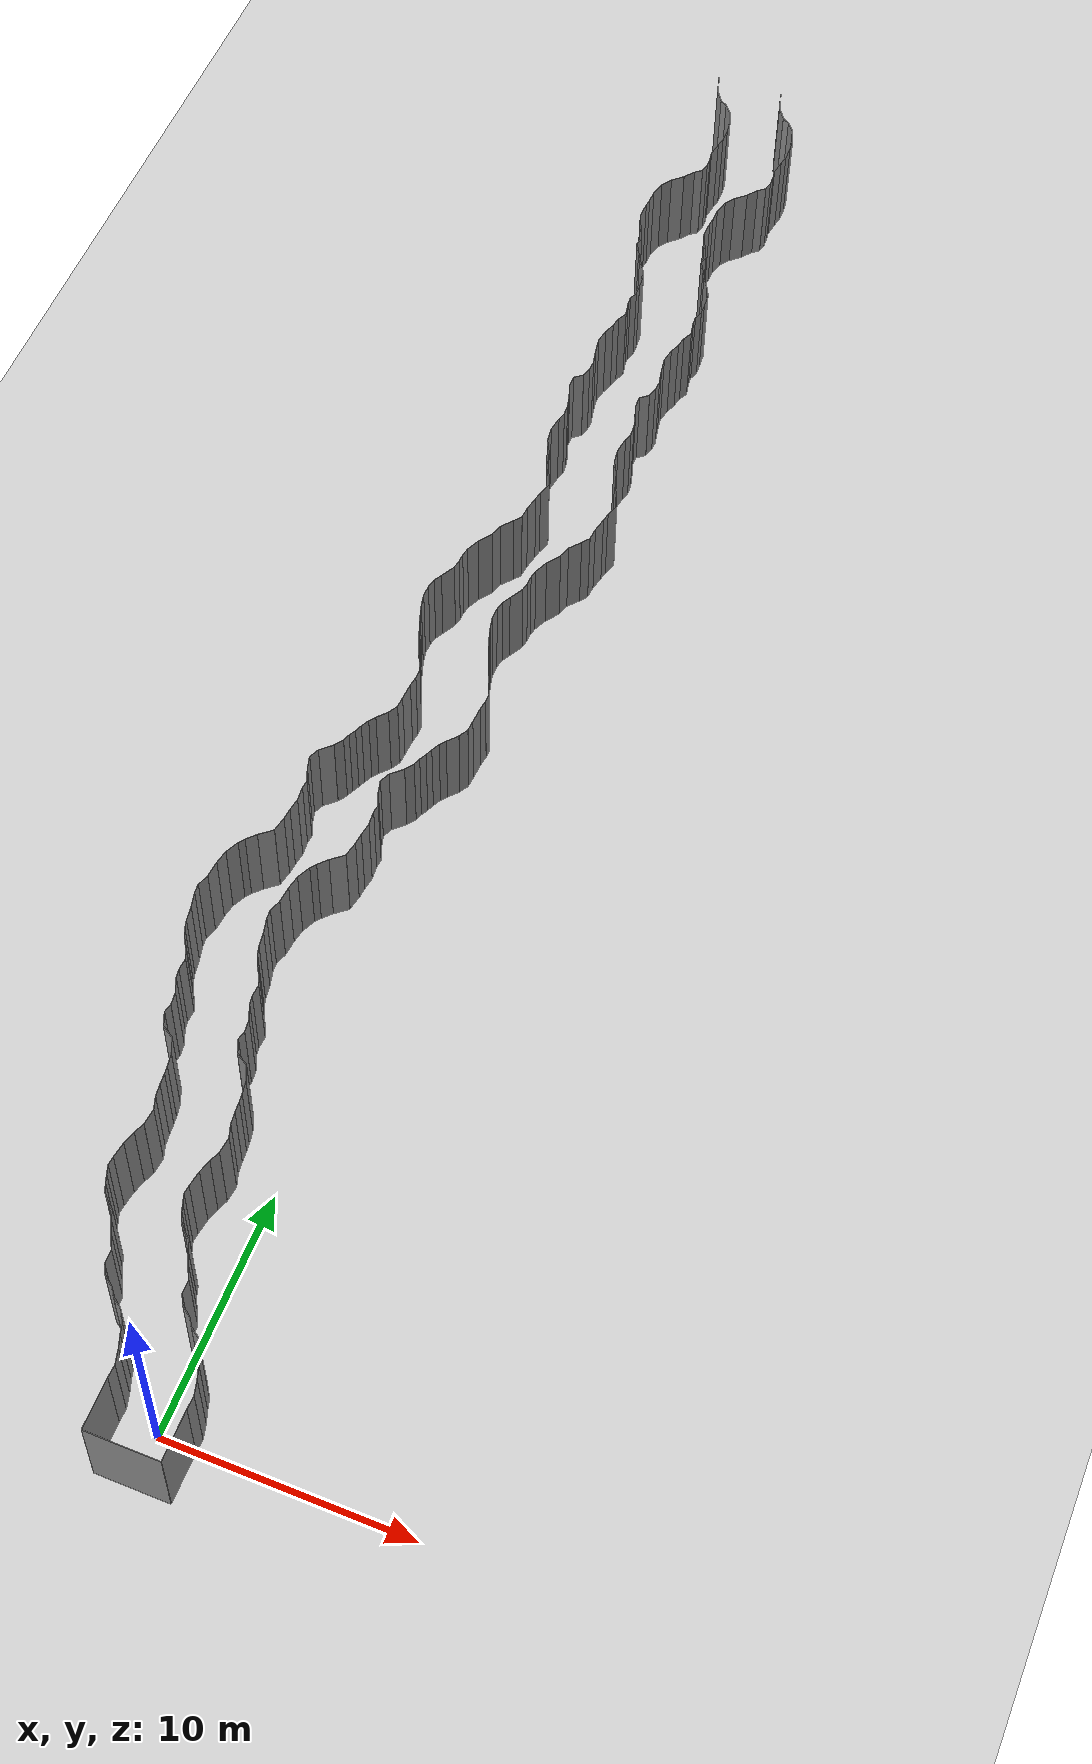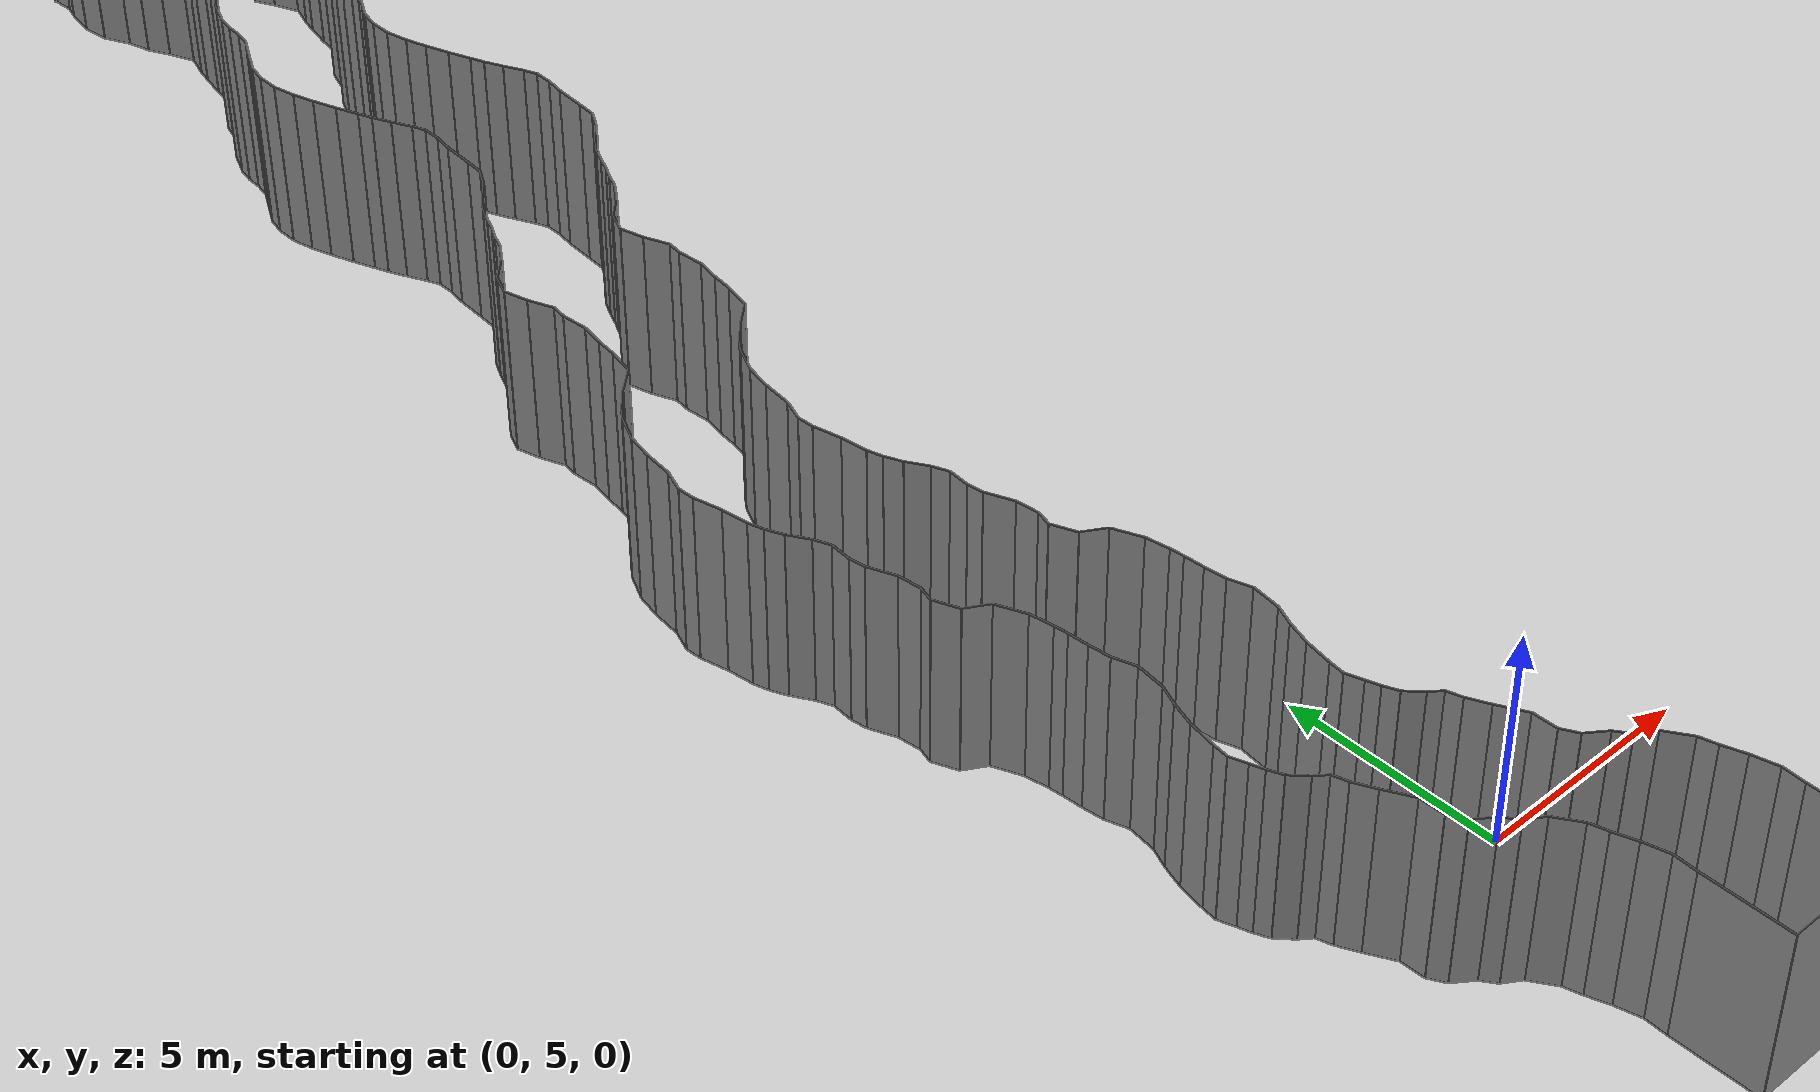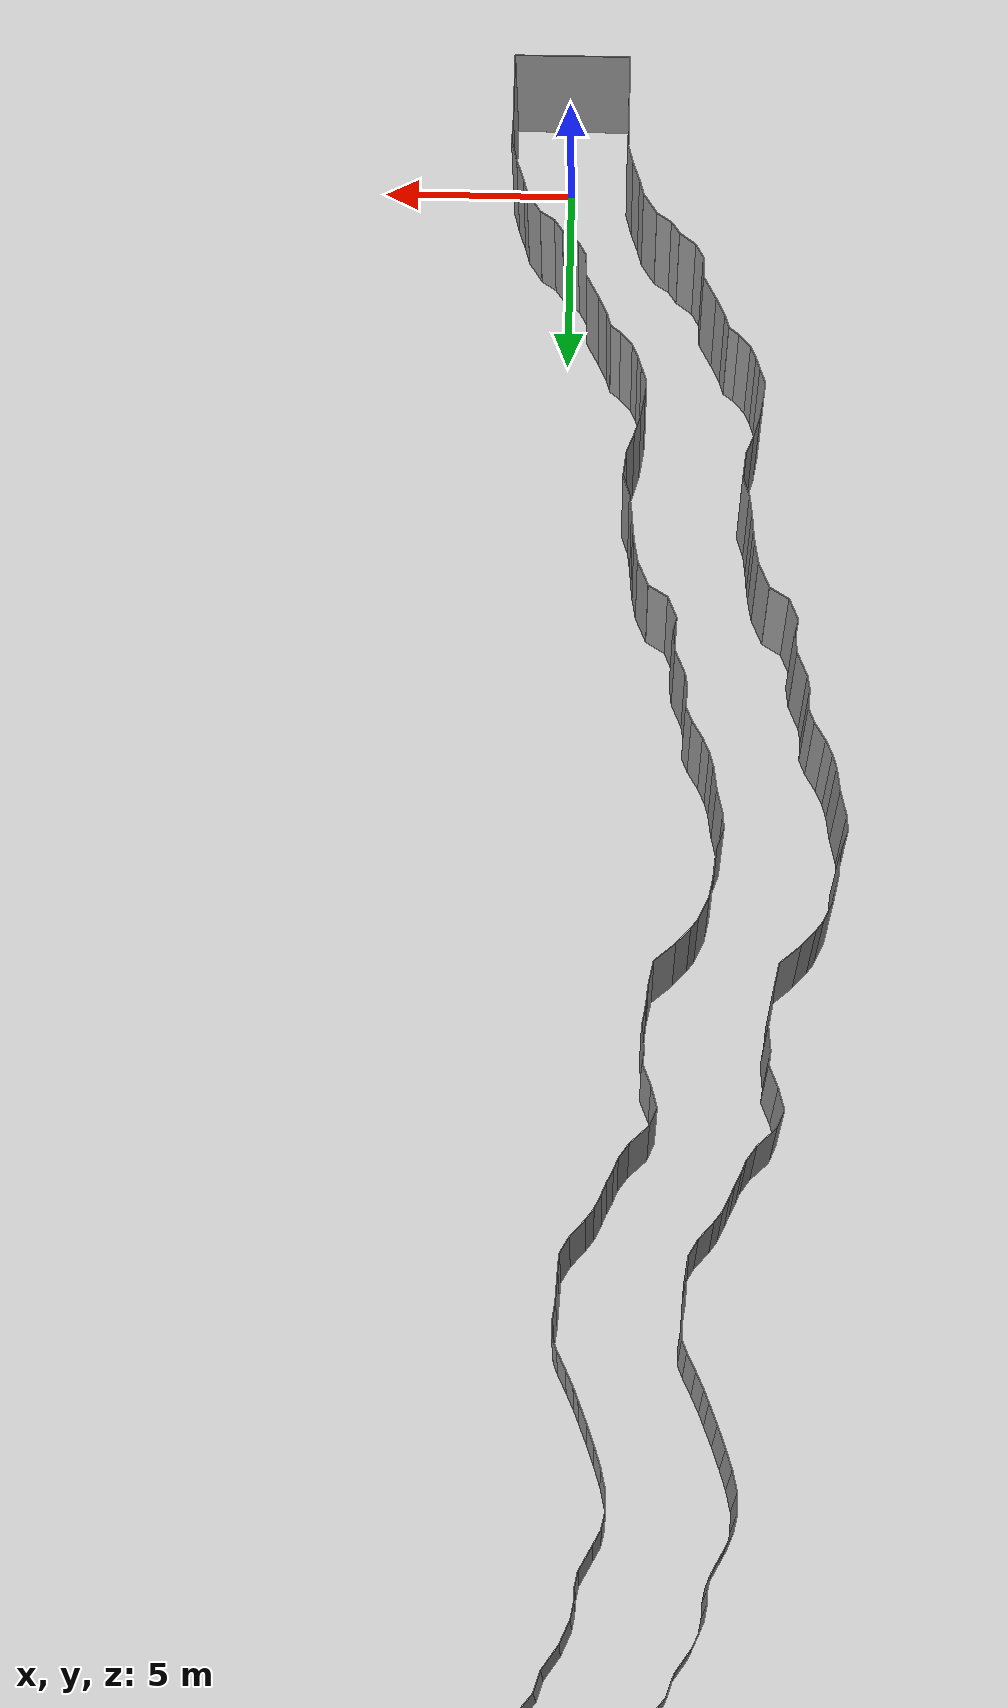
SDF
<sdf version="1.6">
 <world name="default">
  <light name="sun" type="directional">
   <pose>0 0 10 0 -0 0</pose>
   <diffuse>0.8 0.8 0.8 1</diffuse>
   <specular>0.2 0.2 0.2 1</specular>
   <attenuation>
    <range>1000</range>
    <constant>0.9</constant>
    <linear>0.01</linear>
    <quadratic>0.001</quadratic>
   </attenuation>
   <direction>-0.5 0.1 -0.9</direction>
  </light>
  <model name="ground_plane">
   <static>1</static>
   <link name="link">
    <collision name="collision">
     <geometry><plane><normal>0 0 1</normal><size>200 200</size></plane></geometry>
     <surface><friction><ode><mu>100</mu><mu2>50</mu2></ode></friction></surface>
    </collision>
    <visual name="visual">
     <cast_shadows>0</cast_shadows>
     <geometry><plane><normal>0 0 1</normal><size>200 200</size></plane></geometry>
     <material>
      <script><uri>file://media/materials/scripts/gazebo.material</uri><name>Gazebo/Grey</name></script>
     </material>
    </visual>
   </link>
   <pose>0 100 0 0 -0 0</pose>
  </model>
  <gravity>0 0 -9.8</gravity>
  <magnetic_field>6e-06 2.3e-05 -4.2e-05</magnetic_field>
  <atmosphere type="adiabatic"/>
  <physics default="0" name="default_physics" type="ode">
   <max_step_size>0.001</max_step_size>
   <real_time_factor>1</real_time_factor>
   <real_time_update_rate>1000</real_time_update_rate>
  </physics>
  <scene><ambient>0.4 0.4 0.4 1</ambient><background>0.7 0.7 0.7 1</background><shadows>1</shadows></scene>
  <spherical_coordinates>
   <surface_model>EARTH_WGS84</surface_model>
   <latitude_deg>0</latitude_deg>
   <longitude_deg>0</longitude_deg>
   <elevation>0</elevation>
   <heading_deg>0</heading_deg>
  </spherical_coordinates>
  <model name="wall_back">
   <static>1</static>
   <pose>0.0 -2 2 0.0 0 0.0</pose>
   <link name="link">
    <collision name="collision"><geometry><box><size>3 0.02 4</size></box></geometry></collision>
    <visual name="visual">
     <material>
      <script><name>Gazebo/Grey</name><uri>file://media/materials/scripts/gazebo.material</uri></script>
     </material>
     <geometry><box><size>3 0.02 4</size></box></geometry>
    </visual>
   </link>
  </model>
  <model name="wall_left">
   <static>1</static>
   <pose>1.5 -1 2 0 0 0.00</pose>
   <link name="link">
    <collision name="collision"><geometry><box><size>0.02 2 4</size></box></geometry></collision>
    <visual name="visual">
     <material>
      <script><name>Gazebo/Grey</name><uri>file://media/materials/scripts/gazebo.material</uri></script>
     </material>
     <geometry><box><size>0.02 2 4</size></box></geometry>
    </visual>
   </link>
  </model>
  <model name="wall_right">
   <static>1</static>
   <pose>-1.5 -1 2 0 0 0.00</pose>
   <link name="link">
    <collision name="collision"><geometry><box><size>0.02 2 4</size></box></geometry></collision>
    <visual name="visual">
     <material>
      <script><name>Gazebo/Grey</name><uri>file://media/materials/scripts/gazebo.material</uri></script>
     </material>
     <geometry><box><size>0.02 2 4</size></box></geometry>
    </visual>
   </link>
  </model>
  <model name="wall_0">
   <static>1</static>
   <pose>-1.488196250125821 0.2607669083539488 2 0 0 -0.045234642740819266</pose>
   <link name="link">
    <collision name="collision"><geometry><box><size>0.02 0.522067846179 4</size></box></geometry></collision>
    <visual name="visual">
     <material>
      <script><name>Gazebo/Grey</name><uri>file://media/materials/scripts/gazebo.material</uri></script>
     </material>
     <geometry><box><size>0.02 0.522067846179 4</size></box></geometry>
    </visual>
   </link>
  </model>
  <model name="wall_1">
   <static>1</static>
   <pose>1.511803749874179 0.2607669083539488 2 0 0 -0.045234642740819266</pose>
   <link name="link">
    <collision name="collision"><geometry><box><size>0.02 0.522067846179 4</size></box></geometry></collision>
    <visual name="visual">
     <material>
      <script><name>Gazebo/Grey</name><uri>file://media/materials/scripts/gazebo.material</uri></script>
     </material>
     <geometry><box><size>0.02 0.522067846179 4</size></box></geometry>
    </visual>
   </link>
  </model>
  <model name="wall_2">
   <static>1</static>
   <pose>-1.5514209833075863 0.8059642517263823 2 0 0 0.25791011651710716</pose>
   <link name="link">
    <collision name="collision"><geometry><box><size>0.02 0.588319456195 4</size></box></geometry></collision>
    <visual name="visual">
     <material>
      <script><name>Gazebo/Grey</name><uri>file://media/materials/scripts/gazebo.material</uri></script>
     </material>
     <geometry><box><size>0.02 0.588319456195 4</size></box></geometry>
    </visual>
   </link>
  </model>
  <model name="wall_3">
   <static>1</static>
   <pose>1.4485790166924137 0.8059642517263823 2 0 0 0.25791011651710716</pose>
   <link name="link">
    <collision name="collision"><geometry><box><size>0.02 0.588319456195 4</size></box></geometry></collision>
    <visual name="visual">
     <material>
      <script><name>Gazebo/Grey</name><uri>file://media/materials/scripts/gazebo.material</uri></script>
     </material>
     <geometry><box><size>0.02 0.588319456195 4</size></box></geometry>
    </visual>
   </link>
  </model>
  <model name="wall_4">
   <static>1</static>
   <pose>-1.7142074546539643 1.3381656480157638 2 0 0 0.3404026408139336</pose>
   <link name="link">
    <collision name="collision"><geometry><box><size>0.02 0.525706814709 4</size></box></geometry></collision>
    <visual name="visual">
     <material>
      <script><name>Gazebo/Grey</name><uri>file://media/materials/scripts/gazebo.material</uri></script>
     </material>
     <geometry><box><size>0.02 0.525706814709 4</size></box></geometry>
    </visual>
   </link>
  </model>
  <model name="wall_5">
   <static>1</static>
   <pose>1.2857925453460357 1.3381656480157638 2 0 0 0.3404026408139336</pose>
   <link name="link">
    <collision name="collision"><geometry><box><size>0.02 0.525706814709 4</size></box></geometry></collision>
    <visual name="visual">
     <material>
      <script><name>Gazebo/Grey</name><uri>file://media/materials/scripts/gazebo.material</uri></script>
     </material>
     <geometry><box><size>0.02 0.525706814709 4</size></box></geometry>
    </visual>
   </link>
  </model>
  <model name="wall_6">
   <static>1</static>
   <pose>-1.8568225131044054 1.7834236534758765 2 0 0 0.27094477200006256</pose>
   <link name="link">
    <collision name="collision"><geometry><box><size>0.02 0.40992892442 4</size></box></geometry></collision>
    <visual name="visual">
     <material>
      <script><name>Gazebo/Grey</name><uri>file://media/materials/scripts/gazebo.material</uri></script>
     </material>
     <geometry><box><size>0.02 0.40992892442 4</size></box></geometry>
    </visual>
   </link>
  </model>
  <model name="wall_7">
   <static>1</static>
   <pose>1.1431774868955946 1.7834236534758765 2 0 0 0.27094477200006256</pose>
   <link name="link">
    <collision name="collision"><geometry><box><size>0.02 0.40992892442 4</size></box></geometry></collision>
    <visual name="visual">
     <material>
      <script><name>Gazebo/Grey</name><uri>file://media/materials/scripts/gazebo.material</uri></script>
     </material>
     <geometry><box><size>0.02 0.40992892442 4</size></box></geometry>
    </visual>
   </link>
  </model>
  <model name="wall_8">
   <static>1</static>
   <pose>-2.0858675047094546 2.2504126137847265 2 0 0 0.573792885363055</pose>
   <link name="link">
    <collision name="collision"><geometry><box><size>0.02 0.64178723817 4</size></box></geometry></collision>
    <visual name="visual">
     <material>
      <script><name>Gazebo/Grey</name><uri>file://media/materials/scripts/gazebo.material</uri></script>
     </material>
     <geometry><box><size>0.02 0.64178723817 4</size></box></geometry>
    </visual>
   </link>
  </model>
  <model name="wall_9">
   <static>1</static>
   <pose>0.9141324952905454 2.2504126137847265 2 0 0 0.573792885363055</pose>
   <link name="link">
    <collision name="collision"><geometry><box><size>0.02 0.64178723817 4</size></box></geometry></collision>
    <visual name="visual">
     <material>
      <script><name>Gazebo/Grey</name><uri>file://media/materials/scripts/gazebo.material</uri></script>
     </material>
     <geometry><box><size>0.02 0.64178723817 4</size></box></geometry>
    </visual>
   </link>
  </model>
  <model name="wall_10">
   <static>1</static>
   <pose>-2.448899243307415 2.645589367669755 2 0 0 0.9836045022743397</pose>
   <link name="link">
    <collision name="collision"><geometry><box><size>0.02 0.453678970746 4</size></box></geometry></collision>
    <visual name="visual">
     <material>
      <script><name>Gazebo/Grey</name><uri>file://media/materials/scripts/gazebo.material</uri></script>
     </material>
     <geometry><box><size>0.02 0.453678970746 4</size></box></geometry>
    </visual>
   </link>
  </model>
  <model name="wall_11">
   <static>1</static>
   <pose>0.551100756692585 2.645589367669755 2 0 0 0.9836045022743397</pose>
   <link name="link">
    <collision name="collision"><geometry><box><size>0.02 0.453678970746 4</size></box></geometry></collision>
    <visual name="visual">
     <material>
      <script><name>Gazebo/Grey</name><uri>file://media/materials/scripts/gazebo.material</uri></script>
     </material>
     <geometry><box><size>0.02 0.453678970746 4</size></box></geometry>
    </visual>
   </link>
  </model>
  <model name="wall_12">
   <static>1</static>
   <pose>-2.7448915006535177 2.926327362351517 2 0 0 0.6046592441304547</pose>
   <link name="link">
    <collision name="collision"><geometry><box><size>0.02 0.376963504168 4</size></box></geometry></collision>
    <visual name="visual">
     <material>
      <script><name>Gazebo/Grey</name><uri>file://media/materials/scripts/gazebo.material</uri></script>
     </material>
     <geometry><box><size>0.02 0.376963504168 4</size></box></geometry>
    </visual>
   </link>
  </model>
  <model name="wall_13">
   <static>1</static>
   <pose>0.2551084993464823 2.926327362351517 2 0 0 0.6046592441304547</pose>
   <link name="link">
    <collision name="collision"><geometry><box><size>0.02 0.376963504168 4</size></box></geometry></collision>
    <visual name="visual">
     <material>
      <script><name>Gazebo/Grey</name><uri>file://media/materials/scripts/gazebo.material</uri></script>
     </material>
     <geometry><box><size>0.02 0.376963504168 4</size></box></geometry>
    </visual>
   </link>
  </model>
  <model name="wall_14">
   <static>1</static>
   <pose>-3.061418504655303 3.240565309927438 2 0 0 0.9207833559223908</pose>
   <link name="link">
    <collision name="collision"><geometry><box><size>0.02 0.526026603753 4</size></box></geometry></collision>
    <visual name="visual">
     <material>
      <script><name>Gazebo/Grey</name><uri>file://media/materials/scripts/gazebo.material</uri></script>
     </material>
     <geometry><box><size>0.02 0.526026603753 4</size></box></geometry>
    </visual>
   </link>
  </model>
  <model name="wall_15">
   <static>1</static>
   <pose>-0.061418504655303074 3.240565309927438 2 0 0 0.9207833559223908</pose>
   <link name="link">
    <collision name="collision"><geometry><box><size>0.02 0.526026603753 4</size></box></geometry></collision>
    <visual name="visual">
     <material>
      <script><name>Gazebo/Grey</name><uri>file://media/materials/scripts/gazebo.material</uri></script>
     </material>
     <geometry><box><size>0.02 0.526026603753 4</size></box></geometry>
    </visual>
   </link>
  </model>
  <model name="wall_16">
   <static>1</static>
   <pose>-3.368975870759927 3.578136511810658 2 0 0 0.5031047319861869</pose>
   <link name="link">
    <collision name="collision"><geometry><box><size>0.02 0.40725597237 4</size></box></geometry></collision>
    <visual name="visual">
     <material>
      <script><name>Gazebo/Grey</name><uri>file://media/materials/scripts/gazebo.material</uri></script>
     </material>
     <geometry><box><size>0.02 0.40725597237 4</size></box></geometry>
    </visual>
   </link>
  </model>
  <model name="wall_17">
   <static>1</static>
   <pose>-0.3689758707599271 3.578136511810658 2 0 0 0.5031047319861869</pose>
   <link name="link">
    <collision name="collision"><geometry><box><size>0.02 0.40725597237 4</size></box></geometry></collision>
    <visual name="visual">
     <material>
      <script><name>Gazebo/Grey</name><uri>file://media/materials/scripts/gazebo.material</uri></script>
     </material>
     <geometry><box><size>0.02 0.40725597237 4</size></box></geometry>
    </visual>
   </link>
  </model>
  <model name="wall_18">
   <static>1</static>
   <pose>-3.473970301201742 4.038109908194635 2 0 0 0.02420047766314063</pose>
   <link name="link">
    <collision name="collision"><geometry><box><size>0.02 0.563318919828 4</size></box></geometry></collision>
    <visual name="visual">
     <material>
      <script><name>Gazebo/Grey</name><uri>file://media/materials/scripts/gazebo.material</uri></script>
     </material>
     <geometry><box><size>0.02 0.563318919828 4</size></box></geometry>
    </visual>
   </link>
  </model>
  <model name="wall_19">
   <static>1</static>
   <pose>-0.4739703012017422 4.038109908194635 2 0 0 0.02420047766314063</pose>
   <link name="link">
    <collision name="collision"><geometry><box><size>0.02 0.563318919828 4</size></box></geometry></collision>
    <visual name="visual">
     <material>
      <script><name>Gazebo/Grey</name><uri>file://media/materials/scripts/gazebo.material</uri></script>
     </material>
     <geometry><box><size>0.02 0.563318919828 4</size></box></geometry>
    </visual>
   </link>
  </model>
  <model name="wall_20">
   <static>1</static>
   <pose>-3.6416938392011042 4.6202592312180615 2 0 0 0.49151705263493883</pose>
   <link name="link">
    <collision name="collision"><geometry><box><size>0.02 0.681865340788 4</size></box></geometry></collision>
    <visual name="visual">
     <material>
      <script><name>Gazebo/Grey</name><uri>file://media/materials/scripts/gazebo.material</uri></script>
     </material>
     <geometry><box><size>0.02 0.681865340788 4</size></box></geometry>
    </visual>
   </link>
  </model>
  <model name="wall_21">
   <static>1</static>
   <pose>-0.6416938392011042 4.6202592312180615 2 0 0 0.49151705263493883</pose>
   <link name="link">
    <collision name="collision"><geometry><box><size>0.02 0.681865340788 4</size></box></geometry></collision>
    <visual name="visual">
     <material>
      <script><name>Gazebo/Grey</name><uri>file://media/materials/scripts/gazebo.material</uri></script>
     </material>
     <geometry><box><size>0.02 0.681865340788 4</size></box></geometry>
    </visual>
   </link>
  </model>
  <model name="wall_22">
   <static>1</static>
   <pose>-3.9141407788428135 5.151917807327713 2 0 0 0.4496899690787338</pose>
   <link name="link">
    <collision name="collision"><geometry><box><size>0.02 0.513193159241 4</size></box></geometry></collision>
    <visual name="visual">
     <material>
      <script><name>Gazebo/Grey</name><uri>file://media/materials/scripts/gazebo.material</uri></script>
     </material>
     <geometry><box><size>0.02 0.513193159241 4</size></box></geometry>
    </visual>
   </link>
  </model>
  <model name="wall_23">
   <static>1</static>
   <pose>-0.9141407788428135 5.151917807327713 2 0 0 0.4496899690787338</pose>
   <link name="link">
    <collision name="collision"><geometry><box><size>0.02 0.513193159241 4</size></box></geometry></collision>
    <visual name="visual">
     <material>
      <script><name>Gazebo/Grey</name><uri>file://media/materials/scripts/gazebo.material</uri></script>
     </material>
     <geometry><box><size>0.02 0.513193159241 4</size></box></geometry>
    </visual>
   </link>
  </model>
  <model name="wall_24">
   <static>1</static>
   <pose>-4.078167008941469 5.551443125008185 2 0 0 0.30207329674196143</pose>
   <link name="link">
    <collision name="collision"><geometry><box><size>0.02 0.352854812505 4</size></box></geometry></collision>
    <visual name="visual">
     <material>
      <script><name>Gazebo/Grey</name><uri>file://media/materials/scripts/gazebo.material</uri></script>
     </material>
     <geometry><box><size>0.02 0.352854812505 4</size></box></geometry>
    </visual>
   </link>
  </model>
  <model name="wall_25">
   <static>1</static>
   <pose>-1.0781670089414694 5.551443125008185 2 0 0 0.30207329674196143</pose>
   <link name="link">
    <collision name="collision"><geometry><box><size>0.02 0.352854812505 4</size></box></geometry></collision>
    <visual name="visual">
     <material>
      <script><name>Gazebo/Grey</name><uri>file://media/materials/scripts/gazebo.material</uri></script>
     </material>
     <geometry><box><size>0.02 0.352854812505 4</size></box></geometry>
    </visual>
   </link>
  </model>
  <model name="wall_26">
   <static>1</static>
   <pose>-4.257138351103639 5.818999568436784 2 0 0 0.9061141826045659</pose>
   <link name="link">
    <collision name="collision"><geometry><box><size>0.02 0.321387554116 4</size></box></geometry></collision>
    <visual name="visual">
     <material>
      <script><name>Gazebo/Grey</name><uri>file://media/materials/scripts/gazebo.material</uri></script>
     </material>
     <geometry><box><size>0.02 0.321387554116 4</size></box></geometry>
    </visual>
   </link>
  </model>
  <model name="wall_27">
   <static>1</static>
   <pose>-1.257138351103639 5.818999568436784 2 0 0 0.9061141826045659</pose>
   <link name="link">
    <collision name="collision"><geometry><box><size>0.02 0.321387554116 4</size></box></geometry></collision>
    <visual name="visual">
     <material>
      <script><name>Gazebo/Grey</name><uri>file://media/materials/scripts/gazebo.material</uri></script>
     </material>
     <geometry><box><size>0.02 0.321387554116 4</size></box></geometry>
    </visual>
   </link>
  </model>
  <model name="wall_28">
   <static>1</static>
   <pose>-4.534588008272247 6.084138800445451 2 0 0 0.7379355639912297</pose>
   <link name="link">
    <collision name="collision"><geometry><box><size>0.02 0.448793259636 4</size></box></geometry></collision>
    <visual name="visual">
     <material>
      <script><name>Gazebo/Grey</name><uri>file://media/materials/scripts/gazebo.material</uri></script>
     </material>
     <geometry><box><size>0.02 0.448793259636 4</size></box></geometry>
    </visual>
   </link>
  </model>
  <model name="wall_29">
   <static>1</static>
   <pose>-1.5345880082722472 6.084138800445451 2 0 0 0.7379355639912297</pose>
   <link name="link">
    <collision name="collision"><geometry><box><size>0.02 0.448793259636 4</size></box></geometry></collision>
    <visual name="visual">
     <material>
      <script><name>Gazebo/Grey</name><uri>file://media/materials/scripts/gazebo.material</uri></script>
     </material>
     <geometry><box><size>0.02 0.448793259636 4</size></box></geometry>
    </visual>
   </link>
  </model>
  <model name="wall_30">
   <static>1</static>
   <pose>-4.754658241283097 6.408069520371159 2 0 0 0.4125145914691693</pose>
   <link name="link">
    <collision name="collision"><geometry><box><size>0.02 0.344735652462 4</size></box></geometry></collision>
    <visual name="visual">
     <material>
      <script><name>Gazebo/Grey</name><uri>file://media/materials/scripts/gazebo.material</uri></script>
     </material>
     <geometry><box><size>0.02 0.344735652462 4</size></box></geometry>
    </visual>
   </link>
  </model>
  <model name="wall_31">
   <static>1</static>
   <pose>-1.7546582412830967 6.408069520371159 2 0 0 0.4125145914691693</pose>
   <link name="link">
    <collision name="collision"><geometry><box><size>0.02 0.344735652462 4</size></box></geometry></collision>
    <visual name="visual">
     <material>
      <script><name>Gazebo/Grey</name><uri>file://media/materials/scripts/gazebo.material</uri></script>
     </material>
     <geometry><box><size>0.02 0.344735652462 4</size></box></geometry>
    </visual>
   </link>
  </model>
  <model name="wall_32">
   <static>1</static>
   <pose>-4.873573770462193 6.714864603163335 2 0 0 0.3228507294330113</pose>
   <link name="link">
    <collision name="collision"><geometry><box><size>0.02 0.313995074398 4</size></box></geometry></collision>
    <visual name="visual">
     <material>
      <script><name>Gazebo/Grey</name><uri>file://media/materials/scripts/gazebo.material</uri></script>
     </material>
     <geometry><box><size>0.02 0.313995074398 4</size></box></geometry>
    </visual>
   </link>
  </model>
  <model name="wall_33">
   <static>1</static>
   <pose>-1.873573770462193 6.714864603163335 2 0 0 0.3228507294330113</pose>
   <link name="link">
    <collision name="collision"><geometry><box><size>0.02 0.313995074398 4</size></box></geometry></collision>
    <visual name="visual">
     <material>
      <script><name>Gazebo/Grey</name><uri>file://media/materials/scripts/gazebo.material</uri></script>
     </material>
     <geometry><box><size>0.02 0.313995074398 4</size></box></geometry>
    </visual>
   </link>
  </model>
  <model name="wall_34">
   <static>1</static>
   <pose>-4.989544463483804 7.051096613824288 2 0 0 0.33947221708006825</pose>
   <link name="link">
    <collision name="collision"><geometry><box><size>0.02 0.397369204275 4</size></box></geometry></collision>
    <visual name="visual">
     <material>
      <script><name>Gazebo/Grey</name><uri>file://media/materials/scripts/gazebo.material</uri></script>
     </material>
     <geometry><box><size>0.02 0.397369204275 4</size></box></geometry>
    </visual>
   </link>
  </model>
  <model name="wall_35">
   <static>1</static>
   <pose>-1.9895444634838038 7.051096613824288 2 0 0 0.33947221708006825</pose>
   <link name="link">
    <collision name="collision"><geometry><box><size>0.02 0.397369204275 4</size></box></geometry></collision>
    <visual name="visual">
     <material>
      <script><name>Gazebo/Grey</name><uri>file://media/materials/scripts/gazebo.material</uri></script>
     </material>
     <geometry><box><size>0.02 0.397369204275 4</size></box></geometry>
    </visual>
   </link>
  </model>
  <model name="wall_36">
   <static>1</static>
   <pose>-5.037757267641564 7.4127555262891525 2 0 0 -0.10259732752561486</pose>
   <link name="link">
    <collision name="collision"><geometry><box><size>0.02 0.350469204426 4</size></box></geometry></collision>
    <visual name="visual">
     <material>
      <script><name>Gazebo/Grey</name><uri>file://media/materials/scripts/gazebo.material</uri></script>
     </material>
     <geometry><box><size>0.02 0.350469204426 4</size></box></geometry>
    </visual>
   </link>
  </model>
  <model name="wall_37">
   <static>1</static>
   <pose>-2.037757267641564 7.4127555262891525 2 0 0 -0.10259732752561486</pose>
   <link name="link">
    <collision name="collision"><geometry><box><size>0.02 0.350469204426 4</size></box></geometry></collision>
    <visual name="visual">
     <material>
      <script><name>Gazebo/Grey</name><uri>file://media/materials/scripts/gazebo.material</uri></script>
     </material>
     <geometry><box><size>0.02 0.350469204426 4</size></box></geometry>
    </visual>
   </link>
  </model>
  <model name="wall_38">
   <static>1</static>
   <pose>-4.9675300686031445 7.903795718262891 2 0 0 -0.16358857263637194</pose>
   <link name="link">
    <collision name="collision"><geometry><box><size>0.02 0.642025673028 4</size></box></geometry></collision>
    <visual name="visual">
     <material>
      <script><name>Gazebo/Grey</name><uri>file://media/materials/scripts/gazebo.material</uri></script>
     </material>
     <geometry><box><size>0.02 0.642025673028 4</size></box></geometry>
    </visual>
   </link>
  </model>
  <model name="wall_39">
   <static>1</static>
   <pose>-1.9675300686031445 7.903795718262891 2 0 0 -0.16358857263637194</pose>
   <link name="link">
    <collision name="collision"><geometry><box><size>0.02 0.642025673028 4</size></box></geometry></collision>
    <visual name="visual">
     <material>
      <script><name>Gazebo/Grey</name><uri>file://media/materials/scripts/gazebo.material</uri></script>
     </material>
     <geometry><box><size>0.02 0.642025673028 4</size></box></geometry>
    </visual>
   </link>
  </model>
  <model name="wall_40">
   <static>1</static>
   <pose>-4.835692520840622 8.486564621160776 2 0 0 -0.29057677057008835</pose>
   <link name="link">
    <collision name="collision"><geometry><box><size>0.02 0.555365272946 4</size></box></geometry></collision>
    <visual name="visual">
     <material>
      <script><name>Gazebo/Grey</name><uri>file://media/materials/scripts/gazebo.material</uri></script>
     </material>
     <geometry><box><size>0.02 0.555365272946 4</size></box></geometry>
    </visual>
   </link>
  </model>
  <model name="wall_41">
   <static>1</static>
   <pose>-1.835692520840622 8.486564621160776 2 0 0 -0.29057677057008835</pose>
   <link name="link">
    <collision name="collision"><geometry><box><size>0.02 0.555365272946 4</size></box></geometry></collision>
    <visual name="visual">
     <material>
      <script><name>Gazebo/Grey</name><uri>file://media/materials/scripts/gazebo.material</uri></script>
     </material>
     <geometry><box><size>0.02 0.555365272946 4</size></box></geometry>
    </visual>
   </link>
  </model>
  <model name="wall_42">
   <static>1</static>
   <pose>-4.667932031960981 8.969724280892786 2 0 0 -0.38587851829317765</pose>
   <link name="link">
    <collision name="collision"><geometry><box><size>0.02 0.468700016477 4</size></box></geometry></collision>
    <visual name="visual">
     <material>
      <script><name>Gazebo/Grey</name><uri>file://media/materials/scripts/gazebo.material</uri></script>
     </material>
     <geometry><box><size>0.02 0.468700016477 4</size></box></geometry>
    </visual>
   </link>
  </model>
  <model name="wall_43">
   <static>1</static>
   <pose>-1.667932031960981 8.969724280892786 2 0 0 -0.38587851829317765</pose>
   <link name="link">
    <collision name="collision"><geometry><box><size>0.02 0.468700016477 4</size></box></geometry></collision>
    <visual name="visual">
     <material>
      <script><name>Gazebo/Grey</name><uri>file://media/materials/scripts/gazebo.material</uri></script>
     </material>
     <geometry><box><size>0.02 0.468700016477 4</size></box></geometry>
    </visual>
   </link>
  </model>
  <model name="wall_44">
   <static>1</static>
   <pose>-4.543004764600705 9.516516062561731 2 0 0 -0.11093815816098244</pose>
   <link name="link">
    <collision name="collision"><geometry><box><size>0.02 0.663426230295 4</size></box></geometry></collision>
    <visual name="visual">
     <material>
      <script><name>Gazebo/Grey</name><uri>file://media/materials/scripts/gazebo.material</uri></script>
     </material>
     <geometry><box><size>0.02 0.663426230295 4</size></box></geometry>
    </visual>
   </link>
  </model>
  <model name="wall_45">
   <static>1</static>
   <pose>-1.5430047646007052 9.516516062561731 2 0 0 -0.11093815816098244</pose>
   <link name="link">
    <collision name="collision"><geometry><box><size>0.02 0.663426230295 4</size></box></geometry></collision>
    <visual name="visual">
     <material>
      <script><name>Gazebo/Grey</name><uri>file://media/materials/scripts/gazebo.material</uri></script>
     </material>
     <geometry><box><size>0.02 0.663426230295 4</size></box></geometry>
    </visual>
   </link>
  </model>
  <model name="wall_46">
   <static>1</static>
   <pose>-4.590894013853502 10.096853778309976 2 0 0 0.32554756393155354</pose>
   <link name="link">
    <collision name="collision"><geometry><box><size>0.02 0.529119087676 4</size></box></geometry></collision>
    <visual name="visual">
     <material>
      <script><name>Gazebo/Grey</name><uri>file://media/materials/scripts/gazebo.material</uri></script>
     </material>
     <geometry><box><size>0.02 0.529119087676 4</size></box></geometry>
    </visual>
   </link>
  </model>
  <model name="wall_47">
   <static>1</static>
   <pose>-1.590894013853502 10.096853778309976 2 0 0 0.32554756393155354</pose>
   <link name="link">
    <collision name="collision"><geometry><box><size>0.02 0.529119087676 4</size></box></geometry></collision>
    <visual name="visual">
     <material>
      <script><name>Gazebo/Grey</name><uri>file://media/materials/scripts/gazebo.material</uri></script>
     </material>
     <geometry><box><size>0.02 0.529119087676 4</size></box></geometry>
    </visual>
   </link>
  </model>
  <model name="wall_48">
   <static>1</static>
   <pose>-4.705753473052596 10.59333963004754 2 0 0 0.12242490149511323</pose>
   <link name="link">
    <collision name="collision"><geometry><box><size>0.02 0.495351699072 4</size></box></geometry></collision>
    <visual name="visual">
     <material>
      <script><name>Gazebo/Grey</name><uri>file://media/materials/scripts/gazebo.material</uri></script>
     </material>
     <geometry><box><size>0.02 0.495351699072 4</size></box></geometry>
    </visual>
   </link>
  </model>
  <model name="wall_49">
   <static>1</static>
   <pose>-1.7057534730525958 10.59333963004754 2 0 0 0.12242490149511323</pose>
   <link name="link">
    <collision name="collision"><geometry><box><size>0.02 0.495351699072 4</size></box></geometry></collision>
    <visual name="visual">
     <material>
      <script><name>Gazebo/Grey</name><uri>file://media/materials/scripts/gazebo.material</uri></script>
     </material>
     <geometry><box><size>0.02 0.495351699072 4</size></box></geometry>
    </visual>
   </link>
  </model>
  <model name="wall_50">
   <static>1</static>
   <pose>-4.754534412797323 11.067776973373455 2 0 0 0.08089785638518006</pose>
   <link name="link">
    <collision name="collision"><geometry><box><size>0.02 0.458730738328 4</size></box></geometry></collision>
    <visual name="visual">
     <material>
      <script><name>Gazebo/Grey</name><uri>file://media/materials/scripts/gazebo.material</uri></script>
     </material>
     <geometry><box><size>0.02 0.458730738328 4</size></box></geometry>
    </visual>
   </link>
  </model>
  <model name="wall_51">
   <static>1</static>
   <pose>-1.754534412797323 11.067776973373455 2 0 0 0.08089785638518006</pose>
   <link name="link">
    <collision name="collision"><geometry><box><size>0.02 0.458730738328 4</size></box></geometry></collision>
    <visual name="visual">
     <material>
      <script><name>Gazebo/Grey</name><uri>file://media/materials/scripts/gazebo.material</uri></script>
     </material>
     <geometry><box><size>0.02 0.458730738328 4</size></box></geometry>
    </visual>
   </link>
  </model>
  <model name="wall_52">
   <static>1</static>
   <pose>-4.790845780968448 11.453694893478593 2 0 0 0.11253041380742397</pose>
   <link name="link">
    <collision name="collision"><geometry><box><size>0.02 0.316607859682 4</size></box></geometry></collision>
    <visual name="visual">
     <material>
      <script><name>Gazebo/Grey</name><uri>file://media/materials/scripts/gazebo.material</uri></script>
     </material>
     <geometry><box><size>0.02 0.316607859682 4</size></box></geometry>
    </visual>
   </link>
  </model>
  <model name="wall_53">
   <static>1</static>
   <pose>-1.7908457809684482 11.453694893478593 2 0 0 0.11253041380742397</pose>
   <link name="link">
    <collision name="collision"><geometry><box><size>0.02 0.316607859682 4</size></box></geometry></collision>
    <visual name="visual">
     <material>
      <script><name>Gazebo/Grey</name><uri>file://media/materials/scripts/gazebo.material</uri></script>
     </material>
     <geometry><box><size>0.02 0.316607859682 4</size></box></geometry>
    </visual>
   </link>
  </model>
  <model name="wall_54">
   <static>1</static>
   <pose>-4.856595626362631 11.875914156889802 2 0 0 0.17914731323933936</pose>
   <link name="link">
    <collision name="collision"><geometry><box><size>0.02 0.538450537303 4</size></box></geometry></collision>
    <visual name="visual">
     <material>
      <script><name>Gazebo/Grey</name><uri>file://media/materials/scripts/gazebo.material</uri></script>
     </material>
     <geometry><box><size>0.02 0.538450537303 4</size></box></geometry>
    </visual>
   </link>
  </model>
  <model name="wall_55">
   <static>1</static>
   <pose>-1.8565956263626306 11.875914156889802 2 0 0 0.17914731323933936</pose>
   <link name="link">
    <collision name="collision"><geometry><box><size>0.02 0.538450537303 4</size></box></geometry></collision>
    <visual name="visual">
     <material>
      <script><name>Gazebo/Grey</name><uri>file://media/materials/scripts/gazebo.material</uri></script>
     </material>
     <geometry><box><size>0.02 0.538450537303 4</size></box></geometry>
    </visual>
   </link>
  </model>
  <model name="wall_56">
   <static>1</static>
   <pose>-5.0413944911102195 12.459744191013744 2 0 0 0.40528447478965723</pose>
   <link name="link">
    <collision name="collision"><geometry><box><size>0.02 0.69405184993 4</size></box></geometry></collision>
    <visual name="visual">
     <material>
      <script><name>Gazebo/Grey</name><uri>file://media/materials/scripts/gazebo.material</uri></script>
     </material>
     <geometry><box><size>0.02 0.69405184993 4</size></box></geometry>
    </visual>
   </link>
  </model>
  <model name="wall_57">
   <static>1</static>
   <pose>-2.0413944911102195 12.459744191013744 2 0 0 0.40528447478965723</pose>
   <link name="link">
    <collision name="collision"><geometry><box><size>0.02 0.69405184993 4</size></box></geometry></collision>
    <visual name="visual">
     <material>
      <script><name>Gazebo/Grey</name><uri>file://media/materials/scripts/gazebo.material</uri></script>
     </material>
     <geometry><box><size>0.02 0.69405184993 4</size></box></geometry>
    </visual>
   </link>
  </model>
  <model name="wall_58">
   <static>1</static>
   <pose>-5.420740802534709 12.927181729237825 2 0 0 1.021296094337982</pose>
   <link name="link">
    <collision name="collision"><geometry><box><size>0.02 0.568773317847 4</size></box></geometry></collision>
    <visual name="visual">
     <material>
      <script><name>Gazebo/Grey</name><uri>file://media/materials/scripts/gazebo.material</uri></script>
     </material>
     <geometry><box><size>0.02 0.568773317847 4</size></box></geometry>
    </visual>
   </link>
  </model>
  <model name="wall_59">
   <static>1</static>
   <pose>-2.4207408025347092 12.927181729237825 2 0 0 1.021296094337982</pose>
   <link name="link">
    <collision name="collision"><geometry><box><size>0.02 0.568773317847 4</size></box></geometry></collision>
    <visual name="visual">
     <material>
      <script><name>Gazebo/Grey</name><uri>file://media/materials/scripts/gazebo.material</uri></script>
     </material>
     <geometry><box><size>0.02 0.568773317847 4</size></box></geometry>
    </visual>
   </link>
  </model>
  <model name="wall_60">
   <static>1</static>
   <pose>-5.777403072547518 13.350445456474777 2 0 0 0.39375655927977804</pose>
   <link name="link">
    <collision name="collision"><geometry><box><size>0.02 0.59501304383 4</size></box></geometry></collision>
    <visual name="visual">
     <material>
      <script><name>Gazebo/Grey</name><uri>file://media/materials/scripts/gazebo.material</uri></script>
     </material>
     <geometry><box><size>0.02 0.59501304383 4</size></box></geometry>
    </visual>
   </link>
  </model>
  <model name="wall_61">
   <static>1</static>
   <pose>-2.777403072547518 13.350445456474777 2 0 0 0.39375655927977804</pose>
   <link name="link">
    <collision name="collision"><geometry><box><size>0.02 0.59501304383 4</size></box></geometry></collision>
    <visual name="visual">
     <material>
      <script><name>Gazebo/Grey</name><uri>file://media/materials/scripts/gazebo.material</uri></script>
     </material>
     <geometry><box><size>0.02 0.59501304383 4</size></box></geometry>
    </visual>
   </link>
  </model>
  <model name="wall_62">
   <static>1</static>
   <pose>-5.8464923272789475 13.798984009160009 2 0 0 -0.2536373217993913</pose>
   <link name="link">
    <collision name="collision"><geometry><box><size>0.02 0.359086393963 4</size></box></geometry></collision>
    <visual name="visual">
     <material>
      <script><name>Gazebo/Grey</name><uri>file://media/materials/scripts/gazebo.material</uri></script>
     </material>
     <geometry><box><size>0.02 0.359086393963 4</size></box></geometry>
    </visual>
   </link>
  </model>
  <model name="wall_63">
   <static>1</static>
   <pose>-2.8464923272789475 13.798984009160009 2 0 0 -0.2536373217993913</pose>
   <link name="link">
    <collision name="collision"><geometry><box><size>0.02 0.359086393963 4</size></box></geometry></collision>
    <visual name="visual">
     <material>
      <script><name>Gazebo/Grey</name><uri>file://media/materials/scripts/gazebo.material</uri></script>
     </material>
     <geometry><box><size>0.02 0.359086393963 4</size></box></geometry>
    </visual>
   </link>
  </model>
  <model name="wall_64">
   <static>1</static>
   <pose>-5.831909891357075 14.231770695221808 2 0 0 0.11711092110660469</pose>
   <link name="link">
    <collision name="collision"><geometry><box><size>0.02 0.521547963837 4</size></box></geometry></collision>
    <visual name="visual">
     <material>
      <script><name>Gazebo/Grey</name><uri>file://media/materials/scripts/gazebo.material</uri></script>
     </material>
     <geometry><box><size>0.02 0.521547963837 4</size></box></geometry>
    </visual>
   </link>
  </model>
  <model name="wall_65">
   <static>1</static>
   <pose>-2.831909891357075 14.231770695221808 2 0 0 0.11711092110660469</pose>
   <link name="link">
    <collision name="collision"><geometry><box><size>0.02 0.521547963837 4</size></box></geometry></collision>
    <visual name="visual">
     <material>
      <script><name>Gazebo/Grey</name><uri>file://media/materials/scripts/gazebo.material</uri></script>
     </material>
     <geometry><box><size>0.02 0.521547963837 4</size></box></geometry>
    </visual>
   </link>
  </model>
  <model name="wall_66">
   <static>1</static>
   <pose>-5.98955943739056 14.793070981324874 2 0 0 0.3982143067383126</pose>
   <link name="link">
    <collision name="collision"><geometry><box><size>0.02 0.655949889586 4</size></box></geometry></collision>
    <visual name="visual">
     <material>
      <script><name>Gazebo/Grey</name><uri>file://media/materials/scripts/gazebo.material</uri></script>
     </material>
     <geometry><box><size>0.02 0.655949889586 4</size></box></geometry>
    </visual>
   </link>
  </model>
  <model name="wall_67">
   <static>1</static>
   <pose>-2.98955943739056 14.793070981324874 2 0 0 0.3982143067383126</pose>
   <link name="link">
    <collision name="collision"><geometry><box><size>0.02 0.655949889586 4</size></box></geometry></collision>
    <visual name="visual">
     <material>
      <script><name>Gazebo/Grey</name><uri>file://media/materials/scripts/gazebo.material</uri></script>
     </material>
     <geometry><box><size>0.02 0.655949889586 4</size></box></geometry>
    </visual>
   </link>
  </model>
  <model name="wall_68">
   <static>1</static>
   <pose>-6.144753242367112 15.270274801998678 2 0 0 0.15883015454837238</pose>
   <link name="link">
    <collision name="collision"><geometry><box><size>0.02 0.354241454302 4</size></box></geometry></collision>
    <visual name="visual">
     <material>
      <script><name>Gazebo/Grey</name><uri>file://media/materials/scripts/gazebo.material</uri></script>
     </material>
     <geometry><box><size>0.02 0.354241454302 4</size></box></geometry>
    </visual>
   </link>
  </model>
  <model name="wall_69">
   <static>1</static>
   <pose>-3.144753242367112 15.270274801998678 2 0 0 0.15883015454837238</pose>
   <link name="link">
    <collision name="collision"><geometry><box><size>0.02 0.354241454302 4</size></box></geometry></collision>
    <visual name="visual">
     <material>
      <script><name>Gazebo/Grey</name><uri>file://media/materials/scripts/gazebo.material</uri></script>
     </material>
     <geometry><box><size>0.02 0.354241454302 4</size></box></geometry>
    </visual>
   </link>
  </model>
  <model name="wall_70">
   <static>1</static>
   <pose>-6.156168831343654 15.692642996915007 2 0 0 -0.06697016872661828</pose>
   <link name="link">
    <collision name="collision"><geometry><box><size>0.02 0.496065790554 4</size></box></geometry></collision>
    <visual name="visual">
     <material>
      <script><name>Gazebo/Grey</name><uri>file://media/materials/scripts/gazebo.material</uri></script>
     </material>
     <geometry><box><size>0.02 0.496065790554 4</size></box></geometry>
    </visual>
   </link>
  </model>
  <model name="wall_71">
   <static>1</static>
   <pose>-3.1561688313436536 15.692642996915007 2 0 0 -0.06697016872661828</pose>
   <link name="link">
    <collision name="collision"><geometry><box><size>0.02 0.496065790554 4</size></box></geometry></collision>
    <visual name="visual">
     <material>
      <script><name>Gazebo/Grey</name><uri>file://media/materials/scripts/gazebo.material</uri></script>
     </material>
     <geometry><box><size>0.02 0.496065790554 4</size></box></geometry>
    </visual>
   </link>
  </model>
  <model name="wall_72">
   <static>1</static>
   <pose>-6.213504606375548 16.121047888354436 2 0 0 0.3879311940219435</pose>
   <link name="link">
    <collision name="collision"><geometry><box><size>0.02 0.390902560778 4</size></box></geometry></collision>
    <visual name="visual">
     <material>
      <script><name>Gazebo/Grey</name><uri>file://media/materials/scripts/gazebo.material</uri></script>
     </material>
     <geometry><box><size>0.02 0.390902560778 4</size></box></geometry>
    </visual>
   </link>
  </model>
  <model name="wall_73">
   <static>1</static>
   <pose>-3.2135046063755484 16.121047888354436 2 0 0 0.3879311940219435</pose>
   <link name="link">
    <collision name="collision"><geometry><box><size>0.02 0.390902560778 4</size></box></geometry></collision>
    <visual name="visual">
     <material>
      <script><name>Gazebo/Grey</name><uri>file://media/materials/scripts/gazebo.material</uri></script>
     </material>
     <geometry><box><size>0.02 0.390902560778 4</size></box></geometry>
    </visual>
   </link>
  </model>
  <model name="wall_74">
   <static>1</static>
   <pose>-6.423159324145948 16.52691575566886 2 0 0 0.5428891475938377</pose>
   <link name="link">
    <collision name="collision"><geometry><box><size>0.02 0.525425583429 4</size></box></geometry></collision>
    <visual name="visual">
     <material>
      <script><name>Gazebo/Grey</name><uri>file://media/materials/scripts/gazebo.material</uri></script>
     </material>
     <geometry><box><size>0.02 0.525425583429 4</size></box></geometry>
    </visual>
   </link>
  </model>
  <model name="wall_75">
   <static>1</static>
   <pose>-3.4231593241459484 16.52691575566886 2 0 0 0.5428891475938377</pose>
   <link name="link">
    <collision name="collision"><geometry><box><size>0.02 0.525425583429 4</size></box></geometry></collision>
    <visual name="visual">
     <material>
      <script><name>Gazebo/Grey</name><uri>file://media/materials/scripts/gazebo.material</uri></script>
     </material>
     <geometry><box><size>0.02 0.525425583429 4</size></box></geometry>
    </visual>
   </link>
  </model>
  <model name="wall_76">
   <static>1</static>
   <pose>-6.642992999649974 16.937795844756664 2 0 0 0.42482014487990305</pose>
   <link name="link">
    <collision name="collision"><geometry><box><size>0.02 0.408160677202 4</size></box></geometry></collision>
    <visual name="visual">
     <material>
      <script><name>Gazebo/Grey</name><uri>file://media/materials/scripts/gazebo.material</uri></script>
     </material>
     <geometry><box><size>0.02 0.408160677202 4</size></box></geometry>
    </visual>
   </link>
  </model>
  <model name="wall_77">
   <static>1</static>
   <pose>-3.642992999649974 16.937795844756664 2 0 0 0.42482014487990305</pose>
   <link name="link">
    <collision name="collision"><geometry><box><size>0.02 0.408160677202 4</size></box></geometry></collision>
    <visual name="visual">
     <material>
      <script><name>Gazebo/Grey</name><uri>file://media/materials/scripts/gazebo.material</uri></script>
     </material>
     <geometry><box><size>0.02 0.408160677202 4</size></box></geometry>
    </visual>
   </link>
  </model>
  <model name="wall_78">
   <static>1</static>
   <pose>-6.776393060284189 17.29553460870994 2 0 0 0.27938444021321307</pose>
   <link name="link">
    <collision name="collision"><geometry><box><size>0.02 0.357457356194 4</size></box></geometry></collision>
    <visual name="visual">
     <material>
      <script><name>Gazebo/Grey</name><uri>file://media/materials/scripts/gazebo.material</uri></script>
     </material>
     <geometry><box><size>0.02 0.357457356194 4</size></box></geometry>
    </visual>
   </link>
  </model>
  <model name="wall_79">
   <static>1</static>
   <pose>-3.776393060284189 17.29553460870994 2 0 0 0.27938444021321307</pose>
   <link name="link">
    <collision name="collision"><geometry><box><size>0.02 0.357457356194 4</size></box></geometry></collision>
    <visual name="visual">
     <material>
      <script><name>Gazebo/Grey</name><uri>file://media/materials/scripts/gazebo.material</uri></script>
     </material>
     <geometry><box><size>0.02 0.357457356194 4</size></box></geometry>
    </visual>
   </link>
  </model>
  <model name="wall_80">
   <static>1</static>
   <pose>-6.869227630001654 17.76519926221746 2 0 0 0.14517021884053985</pose>
   <link name="link">
    <collision name="collision"><geometry><box><size>0.02 0.602065172895 4</size></box></geometry></collision>
    <visual name="visual">
     <material>
      <script><name>Gazebo/Grey</name><uri>file://media/materials/scripts/gazebo.material</uri></script>
     </material>
     <geometry><box><size>0.02 0.602065172895 4</size></box></geometry>
    </visual>
   </link>
  </model>
  <model name="wall_81">
   <static>1</static>
   <pose>-3.869227630001654 17.76519926221746 2 0 0 0.14517021884053985</pose>
   <link name="link">
    <collision name="collision"><geometry><box><size>0.02 0.602065172895 4</size></box></geometry></collision>
    <visual name="visual">
     <material>
      <script><name>Gazebo/Grey</name><uri>file://media/materials/scripts/gazebo.material</uri></script>
     </material>
     <geometry><box><size>0.02 0.602065172895 4</size></box></geometry>
    </visual>
   </link>
  </model>
  <model name="wall_82">
   <static>1</static>
   <pose>-6.989073264993598 18.376267508968926 2 0 0 0.23895203746667829</pose>
   <link name="link">
    <collision name="collision"><geometry><box><size>0.02 0.644723076013 4</size></box></geometry></collision>
    <visual name="visual">
     <material>
      <script><name>Gazebo/Grey</name><uri>file://media/materials/scripts/gazebo.material</uri></script>
     </material>
     <geometry><box><size>0.02 0.644723076013 4</size></box></geometry>
    </visual>
   </link>
  </model>
  <model name="wall_83">
   <static>1</static>
   <pose>-3.989073264993598 18.376267508968926 2 0 0 0.23895203746667829</pose>
   <link name="link">
    <collision name="collision"><geometry><box><size>0.02 0.644723076013 4</size></box></geometry></collision>
    <visual name="visual">
     <material>
      <script><name>Gazebo/Grey</name><uri>file://media/materials/scripts/gazebo.material</uri></script>
     </material>
     <geometry><box><size>0.02 0.644723076013 4</size></box></geometry>
    </visual>
   </link>
  </model>
  <model name="wall_84">
   <static>1</static>
   <pose>-7.077106790539169 18.876067831468667 2 0 0 0.06280922234749874</pose>
   <link name="link">
    <collision name="collision"><geometry><box><size>0.02 0.37393372069 4</size></box></geometry></collision>
    <visual name="visual">
     <material>
      <script><name>Gazebo/Grey</name><uri>file://media/materials/scripts/gazebo.material</uri></script>
     </material>
     <geometry><box><size>0.02 0.37393372069 4</size></box></geometry>
    </visual>
   </link>
  </model>
  <model name="wall_85">
   <static>1</static>
   <pose>-4.077106790539169 18.876067831468667 2 0 0 0.06280922234749874</pose>
   <link name="link">
    <collision name="collision"><geometry><box><size>0.02 0.37393372069 4</size></box></geometry></collision>
    <visual name="visual">
     <material>
      <script><name>Gazebo/Grey</name><uri>file://media/materials/scripts/gazebo.material</uri></script>
     </material>
     <geometry><box><size>0.02 0.37393372069 4</size></box></geometry>
    </visual>
   </link>
  </model>
  <model name="wall_86">
   <static>1</static>
   <pose>-7.003478589189926 19.30421352085573 2 0 0 -0.33970364114893786</pose>
   <link name="link">
    <collision name="collision"><geometry><box><size>0.02 0.512375487982 4</size></box></geometry></collision>
    <visual name="visual">
     <material>
      <script><name>Gazebo/Grey</name><uri>file://media/materials/scripts/gazebo.material</uri></script>
     </material>
     <geometry><box><size>0.02 0.512375487982 4</size></box></geometry>
    </visual>
   </link>
  </model>
  <model name="wall_87">
   <static>1</static>
   <pose>-4.003478589189926 19.30421352085573 2 0 0 -0.33970364114893786</pose>
   <link name="link">
    <collision name="collision"><geometry><box><size>0.02 0.512375487982 4</size></box></geometry></collision>
    <visual name="visual">
     <material>
      <script><name>Gazebo/Grey</name><uri>file://media/materials/scripts/gazebo.material</uri></script>
     </material>
     <geometry><box><size>0.02 0.512375487982 4</size></box></geometry>
    </visual>
   </link>
  </model>
  <model name="wall_88">
   <static>1</static>
   <pose>-6.887422557820664 19.882661755863364 2 0 0 -0.09085114048353095</pose>
   <link name="link">
    <collision name="collision"><geometry><box><size>0.02 0.676591821013 4</size></box></geometry></collision>
    <visual name="visual">
     <material>
      <script><name>Gazebo/Grey</name><uri>file://media/materials/scripts/gazebo.material</uri></script>
     </material>
     <geometry><box><size>0.02 0.676591821013 4</size></box></geometry>
    </visual>
   </link>
  </model>
  <model name="wall_89">
   <static>1</static>
   <pose>-3.8874225578206643 19.882661755863364 2 0 0 -0.09085114048353095</pose>
   <link name="link">
    <collision name="collision"><geometry><box><size>0.02 0.676591821013 4</size></box></geometry></collision>
    <visual name="visual">
     <material>
      <script><name>Gazebo/Grey</name><uri>file://media/materials/scripts/gazebo.material</uri></script>
     </material>
     <geometry><box><size>0.02 0.676591821013 4</size></box></geometry>
    </visual>
   </link>
  </model>
  <model name="wall_90">
   <static>1</static>
   <pose>-6.799874366065468 20.504023033297106 2 0 0 -0.19727311434767117</pose>
   <link name="link">
    <collision name="collision"><geometry><box><size>0.02 0.580173738682 4</size></box></geometry></collision>
    <visual name="visual">
     <material>
      <script><name>Gazebo/Grey</name><uri>file://media/materials/scripts/gazebo.material</uri></script>
     </material>
     <geometry><box><size>0.02 0.580173738682 4</size></box></geometry>
    </visual>
   </link>
  </model>
  <model name="wall_91">
   <static>1</static>
   <pose>-3.7998743660654677 20.504023033297106 2 0 0 -0.19727311434767117</pose>
   <link name="link">
    <collision name="collision"><geometry><box><size>0.02 0.580173738682 4</size></box></geometry></collision>
    <visual name="visual">
     <material>
      <script><name>Gazebo/Grey</name><uri>file://media/materials/scripts/gazebo.material</uri></script>
     </material>
     <geometry><box><size>0.02 0.580173738682 4</size></box></geometry>
    </visual>
   </link>
  </model>
  <model name="wall_92">
   <static>1</static>
   <pose>-6.613866148938064 21.06647991866227 2 0 0 -0.4349146263797148</pose>
   <link name="link">
    <collision name="collision"><geometry><box><size>0.02 0.613065385241 4</size></box></geometry></collision>
    <visual name="visual">
     <material>
      <script><name>Gazebo/Grey</name><uri>file://media/materials/scripts/gazebo.material</uri></script>
     </material>
     <geometry><box><size>0.02 0.613065385241 4</size></box></geometry>
    </visual>
   </link>
  </model>
  <model name="wall_93">
   <static>1</static>
   <pose>-3.6138661489380643 21.06647991866227 2 0 0 -0.4349146263797148</pose>
   <link name="link">
    <collision name="collision"><geometry><box><size>0.02 0.613065385241 4</size></box></geometry></collision>
    <visual name="visual">
     <material>
      <script><name>Gazebo/Grey</name><uri>file://media/materials/scripts/gazebo.material</uri></script>
     </material>
     <geometry><box><size>0.02 0.613065385241 4</size></box></geometry>
    </visual>
   </link>
  </model>
  <model name="wall_94">
   <static>1</static>
   <pose>-6.3945283378572375 21.46519750203156 2 0 0 -0.6416140310875302</pose>
   <link name="link">
    <collision name="collision"><geometry><box><size>0.02 0.301377095944 4</size></box></geometry></collision>
    <visual name="visual">
     <material>
      <script><name>Gazebo/Grey</name><uri>file://media/materials/scripts/gazebo.material</uri></script>
     </material>
     <geometry><box><size>0.02 0.301377095944 4</size></box></geometry>
    </visual>
   </link>
  </model>
  <model name="wall_95">
   <static>1</static>
   <pose>-3.3945283378572375 21.46519750203156 2 0 0 -0.6416140310875302</pose>
   <link name="link">
    <collision name="collision"><geometry><box><size>0.02 0.301377095944 4</size></box></geometry></collision>
    <visual name="visual">
     <material>
      <script><name>Gazebo/Grey</name><uri>file://media/materials/scripts/gazebo.material</uri></script>
     </material>
     <geometry><box><size>0.02 0.301377095944 4</size></box></geometry>
    </visual>
   </link>
  </model>
  <model name="wall_96">
   <static>1</static>
   <pose>-6.1288649390775625 21.773012226696913 2 0 0 -0.7533724899892661</pose>
   <link name="link">
    <collision name="collision"><geometry><box><size>0.02 0.513016460556 4</size></box></geometry></collision>
    <visual name="visual">
     <material>
      <script><name>Gazebo/Grey</name><uri>file://media/materials/scripts/gazebo.material</uri></script>
     </material>
     <geometry><box><size>0.02 0.513016460556 4</size></box></geometry>
    </visual>
   </link>
  </model>
  <model name="wall_97">
   <static>1</static>
   <pose>-3.1288649390775625 21.773012226696913 2 0 0 -0.7533724899892661</pose>
   <link name="link">
    <collision name="collision"><geometry><box><size>0.02 0.513016460556 4</size></box></geometry></collision>
    <visual name="visual">
     <material>
      <script><name>Gazebo/Grey</name><uri>file://media/materials/scripts/gazebo.material</uri></script>
     </material>
     <geometry><box><size>0.02 0.513016460556 4</size></box></geometry>
    </visual>
   </link>
  </model>
  <model name="wall_98">
   <static>1</static>
   <pose>-5.69435812185841 22.177168624840412 2 0 0 -0.8733177553572878</pose>
   <link name="link">
    <collision name="collision"><geometry><box><size>0.02 0.675906142262 4</size></box></geometry></collision>
    <visual name="visual">
     <material>
      <script><name>Gazebo/Grey</name><uri>file://media/materials/scripts/gazebo.material</uri></script>
     </material>
     <geometry><box><size>0.02 0.675906142262 4</size></box></geometry>
    </visual>
   </link>
  </model>
  <model name="wall_99">
   <static>1</static>
   <pose>-2.69435812185841 22.177168624840412 2 0 0 -0.8733177553572878</pose>
   <link name="link">
    <collision name="collision"><geometry><box><size>0.02 0.675906142262 4</size></box></geometry></collision>
    <visual name="visual">
     <material>
      <script><name>Gazebo/Grey</name><uri>file://media/materials/scripts/gazebo.material</uri></script>
     </material>
     <geometry><box><size>0.02 0.675906142262 4</size></box></geometry>
    </visual>
   </link>
  </model>
  <model name="wall_100">
   <static>1</static>
   <pose>-5.37372864919288 22.697723565073453 2 0 0 -0.20025221801266055</pose>
   <link name="link">
    <collision name="collision"><geometry><box><size>0.02 0.619361093434 4</size></box></geometry></collision>
    <visual name="visual">
     <material>
      <script><name>Gazebo/Grey</name><uri>file://media/materials/scripts/gazebo.material</uri></script>
     </material>
     <geometry><box><size>0.02 0.619361093434 4</size></box></geometry>
    </visual>
   </link>
  </model>
  <model name="wall_101">
   <static>1</static>
   <pose>-2.3737286491928797 22.697723565073453 2 0 0 -0.20025221801266055</pose>
   <link name="link">
    <collision name="collision"><geometry><box><size>0.02 0.619361093434 4</size></box></geometry></collision>
    <visual name="visual">
     <material>
      <script><name>Gazebo/Grey</name><uri>file://media/materials/scripts/gazebo.material</uri></script>
     </material>
     <geometry><box><size>0.02 0.619361093434 4</size></box></geometry>
    </visual>
   </link>
  </model>
  <model name="wall_102">
   <static>1</static>
   <pose>-5.290187474983623 23.22880373849609 2 0 0 -0.09610783668805868</pose>
   <link name="link">
    <collision name="collision"><geometry><box><size>0.02 0.45728658191 4</size></box></geometry></collision>
    <visual name="visual">
     <material>
      <script><name>Gazebo/Grey</name><uri>file://media/materials/scripts/gazebo.material</uri></script>
     </material>
     <geometry><box><size>0.02 0.45728658191 4</size></box></geometry>
    </visual>
   </link>
  </model>
  <model name="wall_103">
   <static>1</static>
   <pose>-2.2901874749836226 23.22880373849609 2 0 0 -0.09610783668805868</pose>
   <link name="link">
    <collision name="collision"><geometry><box><size>0.02 0.45728658191 4</size></box></geometry></collision>
    <visual name="visual">
     <material>
      <script><name>Gazebo/Grey</name><uri>file://media/materials/scripts/gazebo.material</uri></script>
     </material>
     <geometry><box><size>0.02 0.45728658191 4</size></box></geometry>
    </visual>
   </link>
  </model>
  <model name="wall_104">
   <static>1</static>
   <pose>-5.223801430676246 23.71541128617367 2 0 0 -0.16993623811035988</pose>
   <link name="link">
    <collision name="collision"><geometry><box><size>0.02 0.525609922196 4</size></box></geometry></collision>
    <visual name="visual">
     <material>
      <script><name>Gazebo/Grey</name><uri>file://media/materials/scripts/gazebo.material</uri></script>
     </material>
     <geometry><box><size>0.02 0.525609922196 4</size></box></geometry>
    </visual>
   </link>
  </model>
  <model name="wall_105">
   <static>1</static>
   <pose>-2.2238014306762457 23.71541128617367 2 0 0 -0.16993623811035988</pose>
   <link name="link">
    <collision name="collision"><geometry><box><size>0.02 0.525609922196 4</size></box></geometry></collision>
    <visual name="visual">
     <material>
      <script><name>Gazebo/Grey</name><uri>file://media/materials/scripts/gazebo.material</uri></script>
     </material>
     <geometry><box><size>0.02 0.525609922196 4</size></box></geometry>
    </visual>
   </link>
  </model>
  <model name="wall_106">
   <static>1</static>
   <pose>-5.208497494413143 24.269785918924747 2 0 0 0.09834765186255229</pose>
   <link name="link">
    <collision name="collision"><geometry><box><size>0.02 0.593578775214 4</size></box></geometry></collision>
    <visual name="visual">
     <material>
      <script><name>Gazebo/Grey</name><uri>file://media/materials/scripts/gazebo.material</uri></script>
     </material>
     <geometry><box><size>0.02 0.593578775214 4</size></box></geometry>
    </visual>
   </link>
  </model>
  <model name="wall_107">
   <static>1</static>
   <pose>-2.208497494413143 24.269785918924747 2 0 0 0.09834765186255229</pose>
   <link name="link">
    <collision name="collision"><geometry><box><size>0.02 0.593578775214 4</size></box></geometry></collision>
    <visual name="visual">
     <material>
      <script><name>Gazebo/Grey</name><uri>file://media/materials/scripts/gazebo.material</uri></script>
     </material>
     <geometry><box><size>0.02 0.593578775214 4</size></box></geometry>
    </visual>
   </link>
  </model>
  <model name="wall_108">
   <static>1</static>
   <pose>-5.216070686729204 24.731080600780842 2 0 0 -0.12925241426592082</pose>
   <link name="link">
    <collision name="collision"><geometry><box><size>0.02 0.334670544321 4</size></box></geometry></collision>
    <visual name="visual">
     <material>
      <script><name>Gazebo/Grey</name><uri>file://media/materials/scripts/gazebo.material</uri></script>
     </material>
     <geometry><box><size>0.02 0.334670544321 4</size></box></geometry>
    </visual>
   </link>
  </model>
  <model name="wall_109">
   <static>1</static>
   <pose>-2.2160706867292044 24.731080600780842 2 0 0 -0.12925241426592082</pose>
   <link name="link">
    <collision name="collision"><geometry><box><size>0.02 0.334670544321 4</size></box></geometry></collision>
    <visual name="visual">
     <material>
      <script><name>Gazebo/Grey</name><uri>file://media/materials/scripts/gazebo.material</uri></script>
     </material>
     <geometry><box><size>0.02 0.334670544321 4</size></box></geometry>
    </visual>
   </link>
  </model>
  <model name="wall_110">
   <static>1</static>
   <pose>-5.307036805033922 25.170395575581715 2 0 0 0.3905070863135746</pose>
   <link name="link">
    <collision name="collision"><geometry><box><size>0.02 0.59126365241 4</size></box></geometry></collision>
    <visual name="visual">
     <material>
      <script><name>Gazebo/Grey</name><uri>file://media/materials/scripts/gazebo.material</uri></script>
     </material>
     <geometry><box><size>0.02 0.59126365241 4</size></box></geometry>
    </visual>
   </link>
  </model>
  <model name="wall_111">
   <static>1</static>
   <pose>-2.3070368050339223 25.170395575581715 2 0 0 0.3905070863135746</pose>
   <link name="link">
    <collision name="collision"><geometry><box><size>0.02 0.59126365241 4</size></box></geometry></collision>
    <visual name="visual">
     <material>
      <script><name>Gazebo/Grey</name><uri>file://media/materials/scripts/gazebo.material</uri></script>
     </material>
     <geometry><box><size>0.02 0.59126365241 4</size></box></geometry>
    </visual>
   </link>
  </model>
  <model name="wall_112">
   <static>1</static>
   <pose>-5.491503649368458 25.709231340020807 2 0 0 0.264617980472067</pose>
   <link name="link">
    <collision name="collision"><geometry><box><size>0.02 0.550066942442 4</size></box></geometry></collision>
    <visual name="visual">
     <material>
      <script><name>Gazebo/Grey</name><uri>file://media/materials/scripts/gazebo.material</uri></script>
     </material>
     <geometry><box><size>0.02 0.550066942442 4</size></box></geometry>
    </visual>
   </link>
  </model>
  <model name="wall_113">
   <static>1</static>
   <pose>-2.4915036493684584 25.709231340020807 2 0 0 0.264617980472067</pose>
   <link name="link">
    <collision name="collision"><geometry><box><size>0.02 0.550066942442 4</size></box></geometry></collision>
    <visual name="visual">
     <material>
      <script><name>Gazebo/Grey</name><uri>file://media/materials/scripts/gazebo.material</uri></script>
     </material>
     <geometry><box><size>0.02 0.550066942442 4</size></box></geometry>
    </visual>
   </link>
  </model>
  <model name="wall_114">
   <static>1</static>
   <pose>-5.472813881713269 26.192609194310858 2 0 0 -0.3940995082127415</pose>
   <link name="link">
    <collision name="collision"><geometry><box><size>0.02 0.47201892252 4</size></box></geometry></collision>
    <visual name="visual">
     <material>
      <script><name>Gazebo/Grey</name><uri>file://media/materials/scripts/gazebo.material</uri></script>
     </material>
     <geometry><box><size>0.02 0.47201892252 4</size></box></geometry>
    </visual>
   </link>
  </model>
  <model name="wall_115">
   <static>1</static>
   <pose>-2.472813881713269 26.192609194310858 2 0 0 -0.3940995082127415</pose>
   <link name="link">
    <collision name="collision"><geometry><box><size>0.02 0.47201892252 4</size></box></geometry></collision>
    <visual name="visual">
     <material>
      <script><name>Gazebo/Grey</name><uri>file://media/materials/scripts/gazebo.material</uri></script>
     </material>
     <geometry><box><size>0.02 0.47201892252 4</size></box></geometry>
    </visual>
   </link>
  </model>
  <model name="wall_116">
   <static>1</static>
   <pose>-5.147901301687834 26.63007094709179 2 0 0 -0.8178793373527447</pose>
   <link name="link">
    <collision name="collision"><geometry><box><size>0.02 0.642157679858 4</size></box></geometry></collision>
    <visual name="visual">
     <material>
      <script><name>Gazebo/Grey</name><uri>file://media/materials/scripts/gazebo.material</uri></script>
     </material>
     <geometry><box><size>0.02 0.642157679858 4</size></box></geometry>
    </visual>
   </link>
  </model>
  <model name="wall_117">
   <static>1</static>
   <pose>-2.147901301687834 26.63007094709179 2 0 0 -0.8178793373527447</pose>
   <link name="link">
    <collision name="collision"><geometry><box><size>0.02 0.642157679858 4</size></box></geometry></collision>
    <visual name="visual">
     <material>
      <script><name>Gazebo/Grey</name><uri>file://media/materials/scripts/gazebo.material</uri></script>
     </material>
     <geometry><box><size>0.02 0.642157679858 4</size></box></geometry>
    </visual>
   </link>
  </model>
  <model name="wall_118">
   <static>1</static>
   <pose>-4.7890450467739205 27.029036200676106 2 0 0 -0.6068667843275375</pose>
   <link name="link">
    <collision name="collision"><geometry><box><size>0.02 0.436845914201 4</size></box></geometry></collision>
    <visual name="visual">
     <material>
      <script><name>Gazebo/Grey</name><uri>file://media/materials/scripts/gazebo.material</uri></script>
     </material>
     <geometry><box><size>0.02 0.436845914201 4</size></box></geometry>
    </visual>
   </link>
  </model>
  <model name="wall_119">
   <static>1</static>
   <pose>-1.7890450467739205 27.029036200676106 2 0 0 -0.6068667843275375</pose>
   <link name="link">
    <collision name="collision"><geometry><box><size>0.02 0.436845914201 4</size></box></geometry></collision>
    <visual name="visual">
     <material>
      <script><name>Gazebo/Grey</name><uri>file://media/materials/scripts/gazebo.material</uri></script>
     </material>
     <geometry><box><size>0.02 0.436845914201 4</size></box></geometry>
    </visual>
   </link>
  </model>
  <model name="wall_120">
   <static>1</static>
   <pose>-4.60894440625457 27.352057261787305 2 0 0 -0.36901695267178986</pose>
   <link name="link">
    <collision name="collision"><geometry><box><size>0.02 0.307928934002 4</size></box></geometry></collision>
    <visual name="visual">
     <material>
      <script><name>Gazebo/Grey</name><uri>file://media/materials/scripts/gazebo.material</uri></script>
     </material>
     <geometry><box><size>0.02 0.307928934002 4</size></box></geometry>
    </visual>
   </link>
  </model>
  <model name="wall_121">
   <static>1</static>
   <pose>-1.6089444062545697 27.352057261787305 2 0 0 -0.36901695267178986</pose>
   <link name="link">
    <collision name="collision"><geometry><box><size>0.02 0.307928934002 4</size></box></geometry></collision>
    <visual name="visual">
     <material>
      <script><name>Gazebo/Grey</name><uri>file://media/materials/scripts/gazebo.material</uri></script>
     </material>
     <geometry><box><size>0.02 0.307928934002 4</size></box></geometry>
    </visual>
   </link>
  </model>
  <model name="wall_122">
   <static>1</static>
   <pose>-4.479094506153243 27.63827810688253 2 0 0 -0.4803591890744189</pose>
   <link name="link">
    <collision name="collision"><geometry><box><size>0.02 0.321642390205 4</size></box></geometry></collision>
    <visual name="visual">
     <material>
      <script><name>Gazebo/Grey</name><uri>file://media/materials/scripts/gazebo.material</uri></script>
     </material>
     <geometry><box><size>0.02 0.321642390205 4</size></box></geometry>
    </visual>
   </link>
  </model>
  <model name="wall_123">
   <static>1</static>
   <pose>-1.4790945061532428 27.63827810688253 2 0 0 -0.4803591890744189</pose>
   <link name="link">
    <collision name="collision"><geometry><box><size>0.02 0.321642390205 4</size></box></geometry></collision>
    <visual name="visual">
     <material>
      <script><name>Gazebo/Grey</name><uri>file://media/materials/scripts/gazebo.material</uri></script>
     </material>
     <geometry><box><size>0.02 0.321642390205 4</size></box></geometry>
    </visual>
   </link>
  </model>
  <model name="wall_124">
   <static>1</static>
   <pose>-4.344707527756809 27.927040558132283 2 0 0 -0.3899980315376524</pose>
   <link name="link">
    <collision name="collision"><geometry><box><size>0.02 0.31601254607 4</size></box></geometry></collision>
    <visual name="visual">
     <material>
      <script><name>Gazebo/Grey</name><uri>file://media/materials/scripts/gazebo.material</uri></script>
     </material>
     <geometry><box><size>0.02 0.31601254607 4</size></box></geometry>
    </visual>
   </link>
  </model>
  <model name="wall_125">
   <static>1</static>
   <pose>-1.3447075277568086 27.927040558132283 2 0 0 -0.3899980315376524</pose>
   <link name="link">
    <collision name="collision"><geometry><box><size>0.02 0.31601254607 4</size></box></geometry></collision>
    <visual name="visual">
     <material>
      <script><name>Gazebo/Grey</name><uri>file://media/materials/scripts/gazebo.material</uri></script>
     </material>
     <geometry><box><size>0.02 0.31601254607 4</size></box></geometry>
    </visual>
   </link>
  </model>
  <model name="wall_126">
   <static>1</static>
   <pose>-4.201401265759204 28.24389969364475 2 0 0 -0.4536430027394821</pose>
   <link name="link">
    <collision name="collision"><geometry><box><size>0.02 0.379855014237 4</size></box></geometry></collision>
    <visual name="visual">
     <material>
      <script><name>Gazebo/Grey</name><uri>file://media/materials/scripts/gazebo.material</uri></script>
     </material>
     <geometry><box><size>0.02 0.379855014237 4</size></box></geometry>
    </visual>
   </link>
  </model>
  <model name="wall_127">
   <static>1</static>
   <pose>-1.2014012657592037 28.24389969364475 2 0 0 -0.4536430027394821</pose>
   <link name="link">
    <collision name="collision"><geometry><box><size>0.02 0.379855014237 4</size></box></geometry></collision>
    <visual name="visual">
     <material>
      <script><name>Gazebo/Grey</name><uri>file://media/materials/scripts/gazebo.material</uri></script>
     </material>
     <geometry><box><size>0.02 0.379855014237 4</size></box></geometry>
    </visual>
   </link>
  </model>
  <model name="wall_128">
   <static>1</static>
   <pose>-4.019547175990734 28.544523528545326 2 0 0 -0.6493380972154528</pose>
   <link name="link">
    <collision name="collision"><geometry><box><size>0.02 0.326199192135 4</size></box></geometry></collision>
    <visual name="visual">
     <material>
      <script><name>Gazebo/Grey</name><uri>file://media/materials/scripts/gazebo.material</uri></script>
     </material>
     <geometry><box><size>0.02 0.326199192135 4</size></box></geometry>
    </visual>
   </link>
  </model>
  <model name="wall_129">
   <static>1</static>
   <pose>-1.0195471759907342 28.544523528545326 2 0 0 -0.6493380972154528</pose>
   <link name="link">
    <collision name="collision"><geometry><box><size>0.02 0.326199192135 4</size></box></geometry></collision>
    <visual name="visual">
     <material>
      <script><name>Gazebo/Grey</name><uri>file://media/materials/scripts/gazebo.material</uri></script>
     </material>
     <geometry><box><size>0.02 0.326199192135 4</size></box></geometry>
    </visual>
   </link>
  </model>
  <model name="wall_130">
   <static>1</static>
   <pose>-3.738358627075258 28.879678649812906 2 0 0 -0.726983573616719</pose>
   <link name="link">
    <collision name="collision"><geometry><box><size>0.02 0.549394158216 4</size></box></geometry></collision>
    <visual name="visual">
     <material>
      <script><name>Gazebo/Grey</name><uri>file://media/materials/scripts/gazebo.material</uri></script>
     </material>
     <geometry><box><size>0.02 0.549394158216 4</size></box></geometry>
    </visual>
   </link>
  </model>
  <model name="wall_131">
   <static>1</static>
   <pose>-0.7383586270752578 28.879678649812906 2 0 0 -0.726983573616719</pose>
   <link name="link">
    <collision name="collision"><geometry><box><size>0.02 0.549394158216 4</size></box></geometry></collision>
    <visual name="visual">
     <material>
      <script><name>Gazebo/Grey</name><uri>file://media/materials/scripts/gazebo.material</uri></script>
     </material>
     <geometry><box><size>0.02 0.549394158216 4</size></box></geometry>
    </visual>
   </link>
  </model>
  <model name="wall_132">
   <static>1</static>
   <pose>-3.4453840019278794 29.276958081645244 2 0 0 -0.5217880901770836</pose>
   <link name="link">
    <collision name="collision"><geometry><box><size>0.02 0.443013186459 4</size></box></geometry></collision>
    <visual name="visual">
     <material>
      <script><name>Gazebo/Grey</name><uri>file://media/materials/scripts/gazebo.material</uri></script>
     </material>
     <geometry><box><size>0.02 0.443013186459 4</size></box></geometry>
    </visual>
   </link>
  </model>
  <model name="wall_133">
   <static>1</static>
   <pose>-0.4453840019278794 29.276958081645244 2 0 0 -0.5217880901770836</pose>
   <link name="link">
    <collision name="collision"><geometry><box><size>0.02 0.443013186459 4</size></box></geometry></collision>
    <visual name="visual">
     <material>
      <script><name>Gazebo/Grey</name><uri>file://media/materials/scripts/gazebo.material</uri></script>
     </material>
     <geometry><box><size>0.02 0.443013186459 4</size></box></geometry>
    </visual>
   </link>
  </model>
  <model name="wall_134">
   <static>1</static>
   <pose>-3.3212787021667136 29.688581401991005 2 0 0 -0.062305321101703955</pose>
   <link name="link">
    <collision name="collision"><geometry><box><size>0.02 0.440039347174 4</size></box></geometry></collision>
    <visual name="visual">
     <material>
      <script><name>Gazebo/Grey</name><uri>file://media/materials/scripts/gazebo.material</uri></script>
     </material>
     <geometry><box><size>0.02 0.440039347174 4</size></box></geometry>
    </visual>
   </link>
  </model>
  <model name="wall_135">
   <static>1</static>
   <pose>-0.3212787021667136 29.688581401991005 2 0 0 -0.062305321101703955</pose>
   <link name="link">
    <collision name="collision"><geometry><box><size>0.02 0.440039347174 4</size></box></geometry></collision>
    <visual name="visual">
     <material>
      <script><name>Gazebo/Grey</name><uri>file://media/materials/scripts/gazebo.material</uri></script>
     </material>
     <geometry><box><size>0.02 0.440039347174 4</size></box></geometry>
    </visual>
   </link>
  </model>
  <model name="wall_136">
   <static>1</static>
   <pose>-3.2886567886294014 30.25486236291947 2 0 0 -0.0545263091162888</pose>
   <link name="link">
    <collision name="collision"><geometry><box><size>0.02 0.694408427959 4</size></box></geometry></collision>
    <visual name="visual">
     <material>
      <script><name>Gazebo/Grey</name><uri>file://media/materials/scripts/gazebo.material</uri></script>
     </material>
     <geometry><box><size>0.02 0.694408427959 4</size></box></geometry>
    </visual>
   </link>
  </model>
  <model name="wall_137">
   <static>1</static>
   <pose>-0.28865678862940136 30.25486236291947 2 0 0 -0.0545263091162888</pose>
   <link name="link">
    <collision name="collision"><geometry><box><size>0.02 0.694408427959 4</size></box></geometry></collision>
    <visual name="visual">
     <material>
      <script><name>Gazebo/Grey</name><uri>file://media/materials/scripts/gazebo.material</uri></script>
     </material>
     <geometry><box><size>0.02 0.694408427959 4</size></box></geometry>
    </visual>
   </link>
  </model>
  <model name="wall_138">
   <static>1</static>
   <pose>-3.240224388154447 30.807769987212932 2 0 0 -0.14213512514221402</pose>
   <link name="link">
    <collision name="collision"><geometry><box><size>0.02 0.416640329644 4</size></box></geometry></collision>
    <visual name="visual">
     <material>
      <script><name>Gazebo/Grey</name><uri>file://media/materials/scripts/gazebo.material</uri></script>
     </material>
     <geometry><box><size>0.02 0.416640329644 4</size></box></geometry>
    </visual>
   </link>
  </model>
  <model name="wall_139">
   <static>1</static>
   <pose>-0.2402243881544468 30.807769987212932 2 0 0 -0.14213512514221402</pose>
   <link name="link">
    <collision name="collision"><geometry><box><size>0.02 0.416640329644 4</size></box></geometry></collision>
    <visual name="visual">
     <material>
      <script><name>Gazebo/Grey</name><uri>file://media/materials/scripts/gazebo.material</uri></script>
     </material>
     <geometry><box><size>0.02 0.416640329644 4</size></box></geometry>
    </visual>
   </link>
  </model>
  <model name="wall_140">
   <static>1</static>
   <pose>-3.2098198051489515 31.21476751364966 2 0 0 -0.004455472092141639</pose>
   <link name="link">
    <collision name="collision"><geometry><box><size>0.02 0.401560194471 4</size></box></geometry></collision>
    <visual name="visual">
     <material>
      <script><name>Gazebo/Grey</name><uri>file://media/materials/scripts/gazebo.material</uri></script>
     </material>
     <geometry><box><size>0.02 0.401560194471 4</size></box></geometry>
    </visual>
   </link>
  </model>
  <model name="wall_141">
   <static>1</static>
   <pose>-0.2098198051489515 31.21476751364966 2 0 0 -0.004455472092141639</pose>
   <link name="link">
    <collision name="collision"><geometry><box><size>0.02 0.401560194471 4</size></box></geometry></collision>
    <visual name="visual">
     <material>
      <script><name>Gazebo/Grey</name><uri>file://media/materials/scripts/gazebo.material</uri></script>
     </material>
     <geometry><box><size>0.02 0.401560194471 4</size></box></geometry>
    </visual>
   </link>
  </model>
  <model name="wall_142">
   <static>1</static>
   <pose>-3.2686446757434298 31.56336298604865 2 0 0 0.38395699123987437</pose>
   <link name="link">
    <collision name="collision"><geometry><box><size>0.02 0.318850344431 4</size></box></geometry></collision>
    <visual name="visual">
     <material>
      <script><name>Gazebo/Grey</name><uri>file://media/materials/scripts/gazebo.material</uri></script>
     </material>
     <geometry><box><size>0.02 0.318850344431 4</size></box></geometry>
    </visual>
   </link>
  </model>
  <model name="wall_143">
   <static>1</static>
   <pose>-0.26864467574342976 31.56336298604865 2 0 0 0.38395699123987437</pose>
   <link name="link">
    <collision name="collision"><geometry><box><size>0.02 0.318850344431 4</size></box></geometry></collision>
    <visual name="visual">
     <material>
      <script><name>Gazebo/Grey</name><uri>file://media/materials/scripts/gazebo.material</uri></script>
     </material>
     <geometry><box><size>0.02 0.318850344431 4</size></box></geometry>
    </visual>
   </link>
  </model>
  <model name="wall_144">
   <static>1</static>
   <pose>-3.4340201296725317 31.927324113654063 2 0 0 0.454666002218015</pose>
   <link name="link">
    <collision name="collision"><geometry><box><size>0.02 0.481170732938 4</size></box></geometry></collision>
    <visual name="visual">
     <material>
      <script><name>Gazebo/Grey</name><uri>file://media/materials/scripts/gazebo.material</uri></script>
     </material>
     <geometry><box><size>0.02 0.481170732938 4</size></box></geometry>
    </visual>
   </link>
  </model>
  <model name="wall_145">
   <static>1</static>
   <pose>-0.4340201296725317 31.927324113654063 2 0 0 0.454666002218015</pose>
   <link name="link">
    <collision name="collision"><geometry><box><size>0.02 0.481170732938 4</size></box></geometry></collision>
    <visual name="visual">
     <material>
      <script><name>Gazebo/Grey</name><uri>file://media/materials/scripts/gazebo.material</uri></script>
     </material>
     <geometry><box><size>0.02 0.481170732938 4</size></box></geometry>
    </visual>
   </link>
  </model>
  <model name="wall_146">
   <static>1</static>
   <pose>-3.6338697060215184 32.346285266523516 2 0 0 0.4347851689013488</pose>
   <link name="link">
    <collision name="collision"><geometry><box><size>0.02 0.447246338384 4</size></box></geometry></collision>
    <visual name="visual">
     <material>
      <script><name>Gazebo/Grey</name><uri>file://media/materials/scripts/gazebo.material</uri></script>
     </material>
     <geometry><box><size>0.02 0.447246338384 4</size></box></geometry>
    </visual>
   </link>
  </model>
  <model name="wall_147">
   <static>1</static>
   <pose>-0.6338697060215184 32.346285266523516 2 0 0 0.4347851689013488</pose>
   <link name="link">
    <collision name="collision"><geometry><box><size>0.02 0.447246338384 4</size></box></geometry></collision>
    <visual name="visual">
     <material>
      <script><name>Gazebo/Grey</name><uri>file://media/materials/scripts/gazebo.material</uri></script>
     </material>
     <geometry><box><size>0.02 0.447246338384 4</size></box></geometry>
    </visual>
   </link>
  </model>
  <model name="wall_148">
   <static>1</static>
   <pose>-3.7892776898225877 32.704849208237995 2 0 0 0.37449090398083174</pose>
   <link name="link">
    <collision name="collision"><geometry><box><size>0.02 0.334689067679 4</size></box></geometry></collision>
    <visual name="visual">
     <material>
      <script><name>Gazebo/Grey</name><uri>file://media/materials/scripts/gazebo.material</uri></script>
     </material>
     <geometry><box><size>0.02 0.334689067679 4</size></box></geometry>
    </visual>
   </link>
  </model>
  <model name="wall_149">
   <static>1</static>
   <pose>-0.7892776898225877 32.704849208237995 2 0 0 0.37449090398083174</pose>
   <link name="link">
    <collision name="collision"><geometry><box><size>0.02 0.334689067679 4</size></box></geometry></collision>
    <visual name="visual">
     <material>
      <script><name>Gazebo/Grey</name><uri>file://media/materials/scripts/gazebo.material</uri></script>
     </material>
     <geometry><box><size>0.02 0.334689067679 4</size></box></geometry>
    </visual>
   </link>
  </model>
  <model name="wall_150">
   <static>1</static>
   <pose>-3.948809260127809 33.109536914038294 2 0 0 0.37613784439058984</pose>
   <link name="link">
    <collision name="collision"><geometry><box><size>0.02 0.535305375152 4</size></box></geometry></collision>
    <visual name="visual">
     <material>
      <script><name>Gazebo/Grey</name><uri>file://media/materials/scripts/gazebo.material</uri></script>
     </material>
     <geometry><box><size>0.02 0.535305375152 4</size></box></geometry>
    </visual>
   </link>
  </model>
  <model name="wall_151">
   <static>1</static>
   <pose>-0.9488092601278089 33.109536914038294 2 0 0 0.37613784439058984</pose>
   <link name="link">
    <collision name="collision"><geometry><box><size>0.02 0.535305375152 4</size></box></geometry></collision>
    <visual name="visual">
     <material>
      <script><name>Gazebo/Grey</name><uri>file://media/materials/scripts/gazebo.material</uri></script>
     </material>
     <geometry><box><size>0.02 0.535305375152 4</size></box></geometry>
    </visual>
   </link>
  </model>
  <model name="wall_152">
   <static>1</static>
   <pose>-4.142674920669686 33.62427240499004 2 0 0 0.3450977192572981</pose>
   <link name="link">
    <collision name="collision"><geometry><box><size>0.02 0.564893428046 4</size></box></geometry></collision>
    <visual name="visual">
     <material>
      <script><name>Gazebo/Grey</name><uri>file://media/materials/scripts/gazebo.material</uri></script>
     </material>
     <geometry><box><size>0.02 0.564893428046 4</size></box></geometry>
    </visual>
   </link>
  </model>
  <model name="wall_153">
   <static>1</static>
   <pose>-1.1426749206696858 33.62427240499004 2 0 0 0.3450977192572981</pose>
   <link name="link">
    <collision name="collision"><geometry><box><size>0.02 0.564893428046 4</size></box></geometry></collision>
    <visual name="visual">
     <material>
      <script><name>Gazebo/Grey</name><uri>file://media/materials/scripts/gazebo.material</uri></script>
     </material>
     <geometry><box><size>0.02 0.564893428046 4</size></box></geometry>
    </visual>
   </link>
  </model>
  <model name="wall_154">
   <static>1</static>
   <pose>-4.315053243607579 34.12826984295776 2 0 0 0.31200446942488325</pose>
   <link name="link">
    <collision name="collision"><geometry><box><size>0.02 0.500573824743 4</size></box></geometry></collision>
    <visual name="visual">
     <material>
      <script><name>Gazebo/Grey</name><uri>file://media/materials/scripts/gazebo.material</uri></script>
     </material>
     <geometry><box><size>0.02 0.500573824743 4</size></box></geometry>
    </visual>
   </link>
  </model>
  <model name="wall_155">
   <static>1</static>
   <pose>-1.3150532436075792 34.12826984295776 2 0 0 0.31200446942488325</pose>
   <link name="link">
    <collision name="collision"><geometry><box><size>0.02 0.500573824743 4</size></box></geometry></collision>
    <visual name="visual">
     <material>
      <script><name>Gazebo/Grey</name><uri>file://media/materials/scripts/gazebo.material</uri></script>
     </material>
     <geometry><box><size>0.02 0.500573824743 4</size></box></geometry>
    </visual>
   </link>
  </model>
  <model name="wall_156">
   <static>1</static>
   <pose>-4.4494578135614935 34.6224325958079 2 0 0 0.2212543486907716</pose>
   <link name="link">
    <collision name="collision"><geometry><box><size>0.02 0.524710185642 4</size></box></geometry></collision>
    <visual name="visual">
     <material>
      <script><name>Gazebo/Grey</name><uri>file://media/materials/scripts/gazebo.material</uri></script>
     </material>
     <geometry><box><size>0.02 0.524710185642 4</size></box></geometry>
    </visual>
   </link>
  </model>
  <model name="wall_157">
   <static>1</static>
   <pose>-1.4494578135614935 34.6224325958079 2 0 0 0.2212543486907716</pose>
   <link name="link">
    <collision name="collision"><geometry><box><size>0.02 0.524710185642 4</size></box></geometry></collision>
    <visual name="visual">
     <material>
      <script><name>Gazebo/Grey</name><uri>file://media/materials/scripts/gazebo.material</uri></script>
     </material>
     <geometry><box><size>0.02 0.524710185642 4</size></box></geometry>
    </visual>
   </link>
  </model>
  <model name="wall_158">
   <static>1</static>
   <pose>-4.505637766828674 35.120834678292425 2 0 0 -0.0057530862084733125</pose>
   <link name="link">
    <collision name="collision"><geometry><box><size>0.02 0.484892892523 4</size></box></geometry></collision>
    <visual name="visual">
     <material>
      <script><name>Gazebo/Grey</name><uri>file://media/materials/scripts/gazebo.material</uri></script>
     </material>
     <geometry><box><size>0.02 0.484892892523 4</size></box></geometry>
    </visual>
   </link>
  </model>
  <model name="wall_159">
   <static>1</static>
   <pose>-1.5056377668286736 35.120834678292425 2 0 0 -0.0057530862084733125</pose>
   <link name="link">
    <collision name="collision"><geometry><box><size>0.02 0.484892892523 4</size></box></geometry></collision>
    <visual name="visual">
     <material>
      <script><name>Gazebo/Grey</name><uri>file://media/materials/scripts/gazebo.material</uri></script>
     </material>
     <geometry><box><size>0.02 0.484892892523 4</size></box></geometry>
    </visual>
   </link>
  </model>
  <model name="wall_160">
   <static>1</static>
   <pose>-4.461434183996032 35.56179589270923 2 0 0 -0.21238869510129402</pose>
   <link name="link">
    <collision name="collision"><geometry><box><size>0.02 0.406163993498 4</size></box></geometry></collision>
    <visual name="visual">
     <material>
      <script><name>Gazebo/Grey</name><uri>file://media/materials/scripts/gazebo.material</uri></script>
     </material>
     <geometry><box><size>0.02 0.406163993498 4</size></box></geometry>
    </visual>
   </link>
  </model>
  <model name="wall_161">
   <static>1</static>
   <pose>-1.4614341839960323 35.56179589270923 2 0 0 -0.21238869510129402</pose>
   <link name="link">
    <collision name="collision"><geometry><box><size>0.02 0.406163993498 4</size></box></geometry></collision>
    <visual name="visual">
     <material>
      <script><name>Gazebo/Grey</name><uri>file://media/materials/scripts/gazebo.material</uri></script>
     </material>
     <geometry><box><size>0.02 0.406163993498 4</size></box></geometry>
    </visual>
   </link>
  </model>
  <model name="wall_162">
   <static>1</static>
   <pose>-4.327039735002604 35.929933251628405 2 0 0 -0.4950951092348704</pose>
   <link name="link">
    <collision name="collision"><geometry><box><size>0.02 0.385530272858 4</size></box></geometry></collision>
    <visual name="visual">
     <material>
      <script><name>Gazebo/Grey</name><uri>file://media/materials/scripts/gazebo.material</uri></script>
     </material>
     <geometry><box><size>0.02 0.385530272858 4</size></box></geometry>
    </visual>
   </link>
  </model>
  <model name="wall_163">
   <static>1</static>
   <pose>-1.3270397350026037 35.929933251628405 2 0 0 -0.4950951092348704</pose>
   <link name="link">
    <collision name="collision"><geometry><box><size>0.02 0.385530272858 4</size></box></geometry></collision>
    <visual name="visual">
     <material>
      <script><name>Gazebo/Grey</name><uri>file://media/materials/scripts/gazebo.material</uri></script>
     </material>
     <geometry><box><size>0.02 0.385530272858 4</size></box></geometry>
    </visual>
   </link>
  </model>
  <model name="wall_164">
   <static>1</static>
   <pose>-4.074682581515594 36.39140293427029 2 0 0 -0.5035094975256917</pose>
   <link name="link">
    <collision name="collision"><geometry><box><size>0.02 0.666406889705 4</size></box></geometry></collision>
    <visual name="visual">
     <material>
      <script><name>Gazebo/Grey</name><uri>file://media/materials/scripts/gazebo.material</uri></script>
     </material>
     <geometry><box><size>0.02 0.666406889705 4</size></box></geometry>
    </visual>
   </link>
  </model>
  <model name="wall_165">
   <static>1</static>
   <pose>-1.074682581515594 36.39140293427029 2 0 0 -0.5035094975256917</pose>
   <link name="link">
    <collision name="collision"><geometry><box><size>0.02 0.666406889705 4</size></box></geometry></collision>
    <visual name="visual">
     <material>
      <script><name>Gazebo/Grey</name><uri>file://media/materials/scripts/gazebo.material</uri></script>
     </material>
     <geometry><box><size>0.02 0.666406889705 4</size></box></geometry>
    </visual>
   </link>
  </model>
  <model name="wall_166">
   <static>1</static>
   <pose>-3.8791648242205845 36.85937122466556 2 0 0 -0.1947890821669191</pose>
   <link name="link">
    <collision name="collision"><geometry><box><size>0.02 0.359024049945 4</size></box></geometry></collision>
    <visual name="visual">
     <material>
      <script><name>Gazebo/Grey</name><uri>file://media/materials/scripts/gazebo.material</uri></script>
     </material>
     <geometry><box><size>0.02 0.359024049945 4</size></box></geometry>
    </visual>
   </link>
  </model>
  <model name="wall_167">
   <static>1</static>
   <pose>-0.8791648242205845 36.85937122466556 2 0 0 -0.1947890821669191</pose>
   <link name="link">
    <collision name="collision"><geometry><box><size>0.02 0.359024049945 4</size></box></geometry></collision>
    <visual name="visual">
     <material>
      <script><name>Gazebo/Grey</name><uri>file://media/materials/scripts/gazebo.material</uri></script>
     </material>
     <geometry><box><size>0.02 0.359024049945 4</size></box></geometry>
    </visual>
   </link>
  </model>
  <model name="wall_168">
   <static>1</static>
   <pose>-3.838874124404291 37.20662528716462 2 0 0 -0.0323862615887805</pose>
   <link name="link">
    <collision name="collision"><geometry><box><size>0.02 0.342453331239 4</size></box></geometry></collision>
    <visual name="visual">
     <material>
      <script><name>Gazebo/Grey</name><uri>file://media/materials/scripts/gazebo.material</uri></script>
     </material>
     <geometry><box><size>0.02 0.342453331239 4</size></box></geometry>
    </visual>
   </link>
  </model>
  <model name="wall_169">
   <static>1</static>
   <pose>-0.838874124404291 37.20662528716462 2 0 0 -0.0323862615887805</pose>
   <link name="link">
    <collision name="collision"><geometry><box><size>0.02 0.342453331239 4</size></box></geometry></collision>
    <visual name="visual">
     <material>
      <script><name>Gazebo/Grey</name><uri>file://media/materials/scripts/gazebo.material</uri></script>
     </material>
     <geometry><box><size>0.02 0.342453331239 4</size></box></geometry>
    </visual>
   </link>
  </model>
  <model name="wall_170">
   <static>1</static>
   <pose>-3.7995660983113764 37.56007034824028 2 0 0 -0.18312581977114464</pose>
   <link name="link">
    <collision name="collision"><geometry><box><size>0.02 0.370816694403 4</size></box></geometry></collision>
    <visual name="visual">
     <material>
      <script><name>Gazebo/Grey</name><uri>file://media/materials/scripts/gazebo.material</uri></script>
     </material>
     <geometry><box><size>0.02 0.370816694403 4</size></box></geometry>
    </visual>
   </link>
  </model>
  <model name="wall_171">
   <static>1</static>
   <pose>-0.7995660983113764 37.56007034824028 2 0 0 -0.18312581977114464</pose>
   <link name="link">
    <collision name="collision"><geometry><box><size>0.02 0.370816694403 4</size></box></geometry></collision>
    <visual name="visual">
     <material>
      <script><name>Gazebo/Grey</name><uri>file://media/materials/scripts/gazebo.material</uri></script>
     </material>
     <geometry><box><size>0.02 0.370816694403 4</size></box></geometry>
    </visual>
   </link>
  </model>
  <model name="wall_172">
   <static>1</static>
   <pose>-3.6425029620017595 38.0218955724752 2 0 0 -0.41544175826559615</pose>
   <link name="link">
    <collision name="collision"><geometry><box><size>0.02 0.61100752861 4</size></box></geometry></collision>
    <visual name="visual">
     <material>
      <script><name>Gazebo/Grey</name><uri>file://media/materials/scripts/gazebo.material</uri></script>
     </material>
     <geometry><box><size>0.02 0.61100752861 4</size></box></geometry>
    </visual>
   </link>
  </model>
  <model name="wall_173">
   <static>1</static>
   <pose>-0.6425029620017595 38.0218955724752 2 0 0 -0.41544175826559615</pose>
   <link name="link">
    <collision name="collision"><geometry><box><size>0.02 0.61100752861 4</size></box></geometry></collision>
    <visual name="visual">
     <material>
      <script><name>Gazebo/Grey</name><uri>file://media/materials/scripts/gazebo.material</uri></script>
     </material>
     <geometry><box><size>0.02 0.61100752861 4</size></box></geometry>
    </visual>
   </link>
  </model>
  <model name="wall_174">
   <static>1</static>
   <pose>-3.3207851174008214 38.58383930220559 2 0 0 -0.6124339987571504</pose>
   <link name="link">
    <collision name="collision"><geometry><box><size>0.02 0.690317787748 4</size></box></geometry></collision>
    <visual name="visual">
     <material>
      <script><name>Gazebo/Grey</name><uri>file://media/materials/scripts/gazebo.material</uri></script>
     </material>
     <geometry><box><size>0.02 0.690317787748 4</size></box></geometry>
    </visual>
   </link>
  </model>
  <model name="wall_175">
   <static>1</static>
   <pose>-0.3207851174008214 38.58383930220559 2 0 0 -0.6124339987571504</pose>
   <link name="link">
    <collision name="collision"><geometry><box><size>0.02 0.690317787748 4</size></box></geometry></collision>
    <visual name="visual">
     <material>
      <script><name>Gazebo/Grey</name><uri>file://media/materials/scripts/gazebo.material</uri></script>
     </material>
     <geometry><box><size>0.02 0.690317787748 4</size></box></geometry>
    </visual>
   </link>
  </model>
  <model name="wall_176">
   <static>1</static>
   <pose>-3.045010539513174 39.11165706740095 2 0 0 -0.3053761179482191</pose>
   <link name="link">
    <collision name="collision"><geometry><box><size>0.02 0.514590211569 4</size></box></geometry></collision>
    <visual name="visual">
     <material>
      <script><name>Gazebo/Grey</name><uri>file://media/materials/scripts/gazebo.material</uri></script>
     </material>
     <geometry><box><size>0.02 0.514590211569 4</size></box></geometry>
    </visual>
   </link>
  </model>
  <model name="wall_177">
   <static>1</static>
   <pose>-0.04501053951317413 39.11165706740095 2 0 0 -0.3053761179482191</pose>
   <link name="link">
    <collision name="collision"><geometry><box><size>0.02 0.514590211569 4</size></box></geometry></collision>
    <visual name="visual">
     <material>
      <script><name>Gazebo/Grey</name><uri>file://media/materials/scripts/gazebo.material</uri></script>
     </material>
     <geometry><box><size>0.02 0.514590211569 4</size></box></geometry>
    </visual>
   </link>
  </model>
  <model name="wall_178">
   <static>1</static>
   <pose>-2.7726440527883627 39.59425690751664 2 0 0 -0.6880742895249002</pose>
   <link name="link">
    <collision name="collision"><geometry><box><size>0.02 0.614156281779 4</size></box></geometry></collision>
    <visual name="visual">
     <material>
      <script><name>Gazebo/Grey</name><uri>file://media/materials/scripts/gazebo.material</uri></script>
     </material>
     <geometry><box><size>0.02 0.614156281779 4</size></box></geometry>
    </visual>
   </link>
  </model>
  <model name="wall_179">
   <static>1</static>
   <pose>0.22735594721163732 39.59425690751664 2 0 0 -0.6880742895249002</pose>
   <link name="link">
    <collision name="collision"><geometry><box><size>0.02 0.614156281779 4</size></box></geometry></collision>
    <visual name="visual">
     <material>
      <script><name>Gazebo/Grey</name><uri>file://media/materials/scripts/gazebo.material</uri></script>
     </material>
     <geometry><box><size>0.02 0.614156281779 4</size></box></geometry>
    </visual>
   </link>
  </model>
  <model name="wall_180">
   <static>1</static>
   <pose>-2.4564026558576098 39.988729432395644 2 0 0 -0.6567296938618015</pose>
   <link name="link">
    <collision name="collision"><geometry><box><size>0.02 0.397134174334 4</size></box></geometry></collision>
    <visual name="visual">
     <material>
      <script><name>Gazebo/Grey</name><uri>file://media/materials/scripts/gazebo.material</uri></script>
     </material>
     <geometry><box><size>0.02 0.397134174334 4</size></box></geometry>
    </visual>
   </link>
  </model>
  <model name="wall_181">
   <static>1</static>
   <pose>0.5435973441423902 39.988729432395644 2 0 0 -0.6567296938618015</pose>
   <link name="link">
    <collision name="collision"><geometry><box><size>0.02 0.397134174334 4</size></box></geometry></collision>
    <visual name="visual">
     <material>
      <script><name>Gazebo/Grey</name><uri>file://media/materials/scripts/gazebo.material</uri></script>
     </material>
     <geometry><box><size>0.02 0.397134174334 4</size></box></geometry>
    </visual>
   </link>
  </model>
  <model name="wall_182">
   <static>1</static>
   <pose>-2.3125439787578617 40.39504041526889 2 0 0 -0.09060749659054476</pose>
   <link name="link">
    <collision name="collision"><geometry><box><size>0.02 0.500146071569 4</size></box></geometry></collision>
    <visual name="visual">
     <material>
      <script><name>Gazebo/Grey</name><uri>file://media/materials/scripts/gazebo.material</uri></script>
     </material>
     <geometry><box><size>0.02 0.500146071569 4</size></box></geometry>
    </visual>
   </link>
  </model>
  <model name="wall_183">
   <static>1</static>
   <pose>0.6874560212421383 40.39504041526889 2 0 0 -0.09060749659054476</pose>
   <link name="link">
    <collision name="collision"><geometry><box><size>0.02 0.500146071569 4</size></box></geometry></collision>
    <visual name="visual">
     <material>
      <script><name>Gazebo/Grey</name><uri>file://media/materials/scripts/gazebo.material</uri></script>
     </material>
     <geometry><box><size>0.02 0.500146071569 4</size></box></geometry>
    </visual>
   </link>
  </model>
  <model name="wall_184">
   <static>1</static>
   <pose>-2.2266220915654666 40.94343411890724 2 0 0 -0.20837278285419442</pose>
   <link name="link">
    <collision name="collision"><geometry><box><size>0.02 0.611929716924 4</size></box></geometry></collision>
    <visual name="visual">
     <material>
      <script><name>Gazebo/Grey</name><uri>file://media/materials/scripts/gazebo.material</uri></script>
     </material>
     <geometry><box><size>0.02 0.611929716924 4</size></box></geometry>
    </visual>
   </link>
  </model>
  <model name="wall_185">
   <static>1</static>
   <pose>0.7733779084345334 40.94343411890724 2 0 0 -0.20837278285419442</pose>
   <link name="link">
    <collision name="collision"><geometry><box><size>0.02 0.611929716924 4</size></box></geometry></collision>
    <visual name="visual">
     <material>
      <script><name>Gazebo/Grey</name><uri>file://media/materials/scripts/gazebo.material</uri></script>
     </material>
     <geometry><box><size>0.02 0.611929716924 4</size></box></geometry>
    </visual>
   </link>
  </model>
  <model name="wall_186">
   <static>1</static>
   <pose>-2.128738098193758 41.40969219846519 2 0 0 -0.2043406867814975</pose>
   <link name="link">
    <collision name="collision"><geometry><box><size>0.02 0.34091595961 4</size></box></geometry></collision>
    <visual name="visual">
     <material>
      <script><name>Gazebo/Grey</name><uri>file://media/materials/scripts/gazebo.material</uri></script>
     </material>
     <geometry><box><size>0.02 0.34091595961 4</size></box></geometry>
    </visual>
   </link>
  </model>
  <model name="wall_187">
   <static>1</static>
   <pose>0.8712619018062422 41.40969219846519 2 0 0 -0.2043406867814975</pose>
   <link name="link">
    <collision name="collision"><geometry><box><size>0.02 0.34091595961 4</size></box></geometry></collision>
    <visual name="visual">
     <material>
      <script><name>Gazebo/Grey</name><uri>file://media/materials/scripts/gazebo.material</uri></script>
     </material>
     <geometry><box><size>0.02 0.34091595961 4</size></box></geometry>
    </visual>
   </link>
  </model>
  <model name="wall_188">
   <static>1</static>
   <pose>-2.0054563466827693 41.852005461859584 2 0 0 -0.3115582514727673</pose>
   <link name="link">
    <collision name="collision"><geometry><box><size>0.02 0.578661811721 4</size></box></geometry></collision>
    <visual name="visual">
     <material>
      <script><name>Gazebo/Grey</name><uri>file://media/materials/scripts/gazebo.material</uri></script>
     </material>
     <geometry><box><size>0.02 0.578661811721 4</size></box></geometry>
    </visual>
   </link>
  </model>
  <model name="wall_189">
   <static>1</static>
   <pose>0.9945436533172307 41.852005461859584 2 0 0 -0.3115582514727673</pose>
   <link name="link">
    <collision name="collision"><geometry><box><size>0.02 0.578661811721 4</size></box></geometry></collision>
    <visual name="visual">
     <material>
      <script><name>Gazebo/Grey</name><uri>file://media/materials/scripts/gazebo.material</uri></script>
     </material>
     <geometry><box><size>0.02 0.578661811721 4</size></box></geometry>
    </visual>
   </link>
  </model>
  <model name="wall_190">
   <static>1</static>
   <pose>-2.042100634272677 42.4193847715467 2 0 0 0.40547946077160735</pose>
   <link name="link">
    <collision name="collision"><geometry><box><size>0.02 0.635484591752 4</size></box></geometry></collision>
    <visual name="visual">
     <material>
      <script><name>Gazebo/Grey</name><uri>file://media/materials/scripts/gazebo.material</uri></script>
     </material>
     <geometry><box><size>0.02 0.635484591752 4</size></box></geometry>
    </visual>
   </link>
  </model>
  <model name="wall_191">
   <static>1</static>
   <pose>0.9578993657273229 42.4193847715467 2 0 0 0.40547946077160735</pose>
   <link name="link">
    <collision name="collision"><geometry><box><size>0.02 0.635484591752 4</size></box></geometry></collision>
    <visual name="visual">
     <material>
      <script><name>Gazebo/Grey</name><uri>file://media/materials/scripts/gazebo.material</uri></script>
     </material>
     <geometry><box><size>0.02 0.635484591752 4</size></box></geometry>
    </visual>
   </link>
  </model>
  <model name="wall_192">
   <static>1</static>
   <pose>-2.292439568281773 42.960722847088384 2 0 0 0.46468103861668975</pose>
   <link name="link">
    <collision name="collision"><geometry><box><size>0.02 0.557875432859 4</size></box></geometry></collision>
    <visual name="visual">
     <material>
      <script><name>Gazebo/Grey</name><uri>file://media/materials/scripts/gazebo.material</uri></script>
     </material>
     <geometry><box><size>0.02 0.557875432859 4</size></box></geometry>
    </visual>
   </link>
  </model>
  <model name="wall_193">
   <static>1</static>
   <pose>0.7075604317182269 42.960722847088384 2 0 0 0.46468103861668975</pose>
   <link name="link">
    <collision name="collision"><geometry><box><size>0.02 0.557875432859 4</size></box></geometry></collision>
    <visual name="visual">
     <material>
      <script><name>Gazebo/Grey</name><uri>file://media/materials/scripts/gazebo.material</uri></script>
     </material>
     <geometry><box><size>0.02 0.557875432859 4</size></box></geometry>
    </visual>
   </link>
  </model>
  <model name="wall_194">
   <static>1</static>
   <pose>-2.491129693867537 43.47578672479157 2 0 0 0.27053140163089406</pose>
   <link name="link">
    <collision name="collision"><geometry><box><size>0.02 0.551464188948 4</size></box></geometry></collision>
    <visual name="visual">
     <material>
      <script><name>Gazebo/Grey</name><uri>file://media/materials/scripts/gazebo.material</uri></script>
     </material>
     <geometry><box><size>0.02 0.551464188948 4</size></box></geometry>
    </visual>
   </link>
  </model>
  <model name="wall_195">
   <static>1</static>
   <pose>0.5088703061324629 43.47578672479157 2 0 0 0.27053140163089406</pose>
   <link name="link">
    <collision name="collision"><geometry><box><size>0.02 0.551464188948 4</size></box></geometry></collision>
    <visual name="visual">
     <material>
      <script><name>Gazebo/Grey</name><uri>file://media/materials/scripts/gazebo.material</uri></script>
     </material>
     <geometry><box><size>0.02 0.551464188948 4</size></box></geometry>
    </visual>
   </link>
  </model>
  <model name="wall_196">
   <static>1</static>
   <pose>-2.711973880012107 44.034313331818126 2 0 0 0.4656808490476996</pose>
   <link name="link">
    <collision name="collision"><geometry><box><size>0.02 0.655440177734 4</size></box></geometry></collision>
    <visual name="visual">
     <material>
      <script><name>Gazebo/Grey</name><uri>file://media/materials/scripts/gazebo.material</uri></script>
     </material>
     <geometry><box><size>0.02 0.655440177734 4</size></box></geometry>
    </visual>
   </link>
  </model>
  <model name="wall_197">
   <static>1</static>
   <pose>0.28802611998789285 44.034313331818126 2 0 0 0.4656808490476996</pose>
   <link name="link">
    <collision name="collision"><geometry><box><size>0.02 0.655440177734 4</size></box></geometry></collision>
    <visual name="visual">
     <material>
      <script><name>Gazebo/Grey</name><uri>file://media/materials/scripts/gazebo.material</uri></script>
     </material>
     <geometry><box><size>0.02 0.655440177734 4</size></box></geometry>
    </visual>
   </link>
  </model>
  <model name="wall_198">
   <static>1</static>
   <pose>-2.899665627789191 44.63312865351976 2 0 0 0.13170447834071963</pose>
   <link name="link">
    <collision name="collision"><geometry><box><size>0.02 0.617330720508 4</size></box></geometry></collision>
    <visual name="visual">
     <material>
      <script><name>Gazebo/Grey</name><uri>file://media/materials/scripts/gazebo.material</uri></script>
     </material>
     <geometry><box><size>0.02 0.617330720508 4</size></box></geometry>
    </visual>
   </link>
  </model>
  <model name="wall_199">
   <static>1</static>
   <pose>0.10033437221080899 44.63312865351976 2 0 0 0.13170447834071963</pose>
   <link name="link">
    <collision name="collision"><geometry><box><size>0.02 0.617330720508 4</size></box></geometry></collision>
    <visual name="visual">
     <material>
      <script><name>Gazebo/Grey</name><uri>file://media/materials/scripts/gazebo.material</uri></script>
     </material>
     <geometry><box><size>0.02 0.617330720508 4</size></box></geometry>
    </visual>
   </link>
  </model>
  <model name="wall_200">
   <static>1</static>
   <pose>-2.8926894104506085 45.262381069368814 2 0 0 -0.14593089362502157</pose>
   <link name="link">
    <collision name="collision"><geometry><box><size>0.02 0.65346621906 4</size></box></geometry></collision>
    <visual name="visual">
     <material>
      <script><name>Gazebo/Grey</name><uri>file://media/materials/scripts/gazebo.material</uri></script>
     </material>
     <geometry><box><size>0.02 0.65346621906 4</size></box></geometry>
    </visual>
   </link>
  </model>
  <model name="wall_201">
   <static>1</static>
   <pose>0.10731058954939154 45.262381069368814 2 0 0 -0.14593089362502157</pose>
   <link name="link">
    <collision name="collision"><geometry><box><size>0.02 0.65346621906 4</size></box></geometry></collision>
    <visual name="visual">
     <material>
      <script><name>Gazebo/Grey</name><uri>file://media/materials/scripts/gazebo.material</uri></script>
     </material>
     <geometry><box><size>0.02 0.65346621906 4</size></box></geometry>
    </visual>
   </link>
  </model>
  <model name="wall_202">
   <static>1</static>
   <pose>-2.7912926008834065 45.756904003118954 2 0 0 -0.3048296614981764</pose>
   <link name="link">
    <collision name="collision"><geometry><box><size>0.02 0.359079616523 4</size></box></geometry></collision>
    <visual name="visual">
     <material>
      <script><name>Gazebo/Grey</name><uri>file://media/materials/scripts/gazebo.material</uri></script>
     </material>
     <geometry><box><size>0.02 0.359079616523 4</size></box></geometry>
    </visual>
   </link>
  </model>
  <model name="wall_203">
   <static>1</static>
   <pose>0.20870739911659353 45.756904003118954 2 0 0 -0.3048296614981764</pose>
   <link name="link">
    <collision name="collision"><geometry><box><size>0.02 0.359079616523 4</size></box></geometry></collision>
    <visual name="visual">
     <material>
      <script><name>Gazebo/Grey</name><uri>file://media/materials/scripts/gazebo.material</uri></script>
     </material>
     <geometry><box><size>0.02 0.359079616523 4</size></box></geometry>
    </visual>
   </link>
  </model>
  <model name="wall_204">
   <static>1</static>
   <pose>-2.7523751308458033 46.14920960713033 2 0 0 0.06761185586232696</pose>
   <link name="link">
    <collision name="collision"><geometry><box><size>0.02 0.443098243297 4</size></box></geometry></collision>
    <visual name="visual">
     <material>
      <script><name>Gazebo/Grey</name><uri>file://media/materials/scripts/gazebo.material</uri></script>
     </material>
     <geometry><box><size>0.02 0.443098243297 4</size></box></geometry>
    </visual>
   </link>
  </model>
  <model name="wall_205">
   <static>1</static>
   <pose>0.24762486915419668 46.14920960713033 2 0 0 0.06761185586232696</pose>
   <link name="link">
    <collision name="collision"><geometry><box><size>0.02 0.443098243297 4</size></box></geometry></collision>
    <visual name="visual">
     <material>
      <script><name>Gazebo/Grey</name><uri>file://media/materials/scripts/gazebo.material</uri></script>
     </material>
     <geometry><box><size>0.02 0.443098243297 4</size></box></geometry>
    </visual>
   </link>
  </model>
  <model name="wall_206">
   <static>1</static>
   <pose>-2.802446100665872 46.5324693255604 2 0 0 0.21310990389237605</pose>
   <link name="link">
    <collision name="collision"><geometry><box><size>0.02 0.3319428346 4</size></box></geometry></collision>
    <visual name="visual">
     <material>
      <script><name>Gazebo/Grey</name><uri>file://media/materials/scripts/gazebo.material</uri></script>
     </material>
     <geometry><box><size>0.02 0.3319428346 4</size></box></geometry>
    </visual>
   </link>
  </model>
  <model name="wall_207">
   <static>1</static>
   <pose>0.19755389933412815 46.5324693255604 2 0 0 0.21310990389237605</pose>
   <link name="link">
    <collision name="collision"><geometry><box><size>0.02 0.3319428346 4</size></box></geometry></collision>
    <visual name="visual">
     <material>
      <script><name>Gazebo/Grey</name><uri>file://media/materials/scripts/gazebo.material</uri></script>
     </material>
     <geometry><box><size>0.02 0.3319428346 4</size></box></geometry>
    </visual>
   </link>
  </model>
  <model name="wall_208">
   <static>1</static>
   <pose>-2.919280490812267 46.953388514761926 2 0 0 0.3060049275418062</pose>
   <link name="link">
    <collision name="collision"><geometry><box><size>0.02 0.542611993081 4</size></box></geometry></collision>
    <visual name="visual">
     <material>
      <script><name>Gazebo/Grey</name><uri>file://media/materials/scripts/gazebo.material</uri></script>
     </material>
     <geometry><box><size>0.02 0.542611993081 4</size></box></geometry>
    </visual>
   </link>
  </model>
  <model name="wall_209">
   <static>1</static>
   <pose>0.08071950918773307 46.953388514761926 2 0 0 0.3060049275418062</pose>
   <link name="link">
    <collision name="collision"><geometry><box><size>0.02 0.542611993081 4</size></box></geometry></collision>
    <visual name="visual">
     <material>
      <script><name>Gazebo/Grey</name><uri>file://media/materials/scripts/gazebo.material</uri></script>
     </material>
     <geometry><box><size>0.02 0.542611993081 4</size></box></geometry>
    </visual>
   </link>
  </model>
  <model name="wall_210">
   <static>1</static>
   <pose>-3.0529548870642444 47.35448068768838 2 0 0 0.34979369279560596</pose>
   <link name="link">
    <collision name="collision"><geometry><box><size>0.02 0.303136459388 4</size></box></geometry></collision>
    <visual name="visual">
     <material>
      <script><name>Gazebo/Grey</name><uri>file://media/materials/scripts/gazebo.material</uri></script>
     </material>
     <geometry><box><size>0.02 0.303136459388 4</size></box></geometry>
    </visual>
   </link>
  </model>
  <model name="wall_211">
   <static>1</static>
   <pose>-0.05295488706424445 47.35448068768838 2 0 0 0.34979369279560596</pose>
   <link name="link">
    <collision name="collision"><geometry><box><size>0.02 0.303136459388 4</size></box></geometry></collision>
    <visual name="visual">
     <material>
      <script><name>Gazebo/Grey</name><uri>file://media/materials/scripts/gazebo.material</uri></script>
     </material>
     <geometry><box><size>0.02 0.303136459388 4</size></box></geometry>
    </visual>
   </link>
  </model>
  <model name="wall_212">
   <static>1</static>
   <pose>-3.1097217375445214 47.7403030544922 2 0 0 0.019813208112904598</pose>
   <link name="link">
    <collision name="collision"><geometry><box><size>0.02 0.486960755196 4</size></box></geometry></collision>
    <visual name="visual">
     <material>
      <script><name>Gazebo/Grey</name><uri>file://media/materials/scripts/gazebo.material</uri></script>
     </material>
     <geometry><box><size>0.02 0.486960755196 4</size></box></geometry>
    </visual>
   </link>
  </model>
  <model name="wall_213">
   <static>1</static>
   <pose>-0.10972173754452141 47.7403030544922 2 0 0 0.019813208112904598</pose>
   <link name="link">
    <collision name="collision"><geometry><box><size>0.02 0.486960755196 4</size></box></geometry></collision>
    <visual name="visual">
     <material>
      <script><name>Gazebo/Grey</name><uri>file://media/materials/scripts/gazebo.material</uri></script>
     </material>
     <geometry><box><size>0.02 0.486960755196 4</size></box></geometry>
    </visual>
   </link>
  </model>
  <model name="wall_214">
   <static>1</static>
   <pose>-2.943529544816595 48.1246244634919 2 0 0 -0.8816903938771686</pose>
   <link name="link">
    <collision name="collision"><geometry><box><size>0.02 0.443152946747 4</size></box></geometry></collision>
    <visual name="visual">
     <material>
      <script><name>Gazebo/Grey</name><uri>file://media/materials/scripts/gazebo.material</uri></script>
     </material>
     <geometry><box><size>0.02 0.443152946747 4</size></box></geometry>
    </visual>
   </link>
  </model>
  <model name="wall_215">
   <static>1</static>
   <pose>0.05647045518340521 48.1246244634919 2 0 0 -0.8816903938771686</pose>
   <link name="link">
    <collision name="collision"><geometry><box><size>0.02 0.443152946747 4</size></box></geometry></collision>
    <visual name="visual">
     <material>
      <script><name>Gazebo/Grey</name><uri>file://media/materials/scripts/gazebo.material</uri></script>
     </material>
     <geometry><box><size>0.02 0.443152946747 4</size></box></geometry>
    </visual>
   </link>
  </model>
  <model name="wall_216">
   <static>1</static>
   <pose>-2.711002390141287 48.46185433263491 2 0 0 -0.3036019314396584</pose>
   <link name="link">
    <collision name="collision"><geometry><box><size>0.02 0.411501781068 4</size></box></geometry></collision>
    <visual name="visual">
     <material>
      <script><name>Gazebo/Grey</name><uri>file://media/materials/scripts/gazebo.material</uri></script>
     </material>
     <geometry><box><size>0.02 0.411501781068 4</size></box></geometry>
    </visual>
   </link>
  </model>
  <model name="wall_217">
   <static>1</static>
   <pose>0.28899760985871303 48.46185433263491 2 0 0 -0.3036019314396584</pose>
   <link name="link">
    <collision name="collision"><geometry><box><size>0.02 0.411501781068 4</size></box></geometry></collision>
    <visual name="visual">
     <material>
      <script><name>Gazebo/Grey</name><uri>file://media/materials/scripts/gazebo.material</uri></script>
     </material>
     <geometry><box><size>0.02 0.411501781068 4</size></box></geometry>
    </visual>
   </link>
  </model>
  <model name="wall_218">
   <static>1</static>
   <pose>-2.6395973024196797 48.85765242258943 2 0 0 -0.049563727883277724</pose>
   <link name="link">
    <collision name="collision"><geometry><box><size>0.02 0.39940456358 4</size></box></geometry></collision>
    <visual name="visual">
     <material>
      <script><name>Gazebo/Grey</name><uri>file://media/materials/scripts/gazebo.material</uri></script>
     </material>
     <geometry><box><size>0.02 0.39940456358 4</size></box></geometry>
    </visual>
   </link>
  </model>
  <model name="wall_219">
   <static>1</static>
   <pose>0.3604026975803203 48.85765242258943 2 0 0 -0.049563727883277724</pose>
   <link name="link">
    <collision name="collision"><geometry><box><size>0.02 0.39940456358 4</size></box></geometry></collision>
    <visual name="visual">
     <material>
      <script><name>Gazebo/Grey</name><uri>file://media/materials/scripts/gazebo.material</uri></script>
     </material>
     <geometry><box><size>0.02 0.39940456358 4</size></box></geometry>
    </visual>
   </link>
  </model>
  <model name="wall_220">
   <static>1</static>
   <pose>-2.7024540921958886 49.383948559591616 2 0 0 0.21901826105031877</pose>
   <link name="link">
    <collision name="collision"><geometry><box><size>0.02 0.669675929863 4</size></box></geometry></collision>
    <visual name="visual">
     <material>
      <script><name>Gazebo/Grey</name><uri>file://media/materials/scripts/gazebo.material</uri></script>
     </material>
     <geometry><box><size>0.02 0.669675929863 4</size></box></geometry>
    </visual>
   </link>
  </model>
  <model name="wall_221">
   <static>1</static>
   <pose>0.2975459078041114 49.383948559591616 2 0 0 0.21901826105031877</pose>
   <link name="link">
    <collision name="collision"><geometry><box><size>0.02 0.669675929863 4</size></box></geometry></collision>
    <visual name="visual">
     <material>
      <script><name>Gazebo/Grey</name><uri>file://media/materials/scripts/gazebo.material</uri></script>
     </material>
     <geometry><box><size>0.02 0.669675929863 4</size></box></geometry>
    </visual>
   </link>
  </model>
  <model name="wall_222">
   <static>1</static>
   <pose>-2.8285108046227343 50.02675698191476 2 0 0 0.16713243163091884</pose>
   <link name="link">
    <collision name="collision"><geometry><box><size>0.02 0.640868608866 4</size></box></geometry></collision>
    <visual name="visual">
     <material>
      <script><name>Gazebo/Grey</name><uri>file://media/materials/scripts/gazebo.material</uri></script>
     </material>
     <geometry><box><size>0.02 0.640868608866 4</size></box></geometry>
    </visual>
   </link>
  </model>
  <model name="wall_223">
   <static>1</static>
   <pose>0.1714891953772657 50.02675698191476 2 0 0 0.16713243163091884</pose>
   <link name="link">
    <collision name="collision"><geometry><box><size>0.02 0.640868608866 4</size></box></geometry></collision>
    <visual name="visual">
     <material>
      <script><name>Gazebo/Grey</name><uri>file://media/materials/scripts/gazebo.material</uri></script>
     </material>
     <geometry><box><size>0.02 0.640868608866 4</size></box></geometry>
    </visual>
   </link>
  </model>
  <model name="wall_224">
   <static>1</static>
   <pose>-2.8286769337761193 50.627891872682405 2 0 0 -0.18423424427518173</pose>
   <link name="link">
    <collision name="collision"><geometry><box><size>0.02 0.580149095409 4</size></box></geometry></collision>
    <visual name="visual">
     <material>
      <script><name>Gazebo/Grey</name><uri>file://media/materials/scripts/gazebo.material</uri></script>
     </material>
     <geometry><box><size>0.02 0.580149095409 4</size></box></geometry>
    </visual>
   </link>
  </model>
  <model name="wall_225">
   <static>1</static>
   <pose>0.17132306622388072 50.627891872682405 2 0 0 -0.18423424427518173</pose>
   <link name="link">
    <collision name="collision"><geometry><box><size>0.02 0.580149095409 4</size></box></geometry></collision>
    <visual name="visual">
     <material>
      <script><name>Gazebo/Grey</name><uri>file://media/materials/scripts/gazebo.material</uri></script>
     </material>
     <geometry><box><size>0.02 0.580149095409 4</size></box></geometry>
    </visual>
   </link>
  </model>
  <model name="wall_226">
   <static>1</static>
   <pose>-2.6917528820557632 51.13423837053062 2 0 0 -0.362101400546652</pose>
   <link name="link">
    <collision name="collision"><geometry><box><size>0.02 0.473036137834 4</size></box></geometry></collision>
    <visual name="visual">
     <material>
      <script><name>Gazebo/Grey</name><uri>file://media/materials/scripts/gazebo.material</uri></script>
     </material>
     <geometry><box><size>0.02 0.473036137834 4</size></box></geometry>
    </visual>
   </link>
  </model>
  <model name="wall_227">
   <static>1</static>
   <pose>0.30824711794423676 51.13423837053062 2 0 0 -0.362101400546652</pose>
   <link name="link">
    <collision name="collision"><geometry><box><size>0.02 0.473036137834 4</size></box></geometry></collision>
    <visual name="visual">
     <material>
      <script><name>Gazebo/Grey</name><uri>file://media/materials/scripts/gazebo.material</uri></script>
     </material>
     <geometry><box><size>0.02 0.473036137834 4</size></box></geometry>
    </visual>
   </link>
  </model>
  <model name="wall_228">
   <static>1</static>
   <pose>-2.563501841455428 51.57859780687657 2 0 0 -0.1966679591682121</pose>
   <link name="link">
    <collision name="collision"><geometry><box><size>0.02 0.455130505683 4</size></box></geometry></collision>
    <visual name="visual">
     <material>
      <script><name>Gazebo/Grey</name><uri>file://media/materials/scripts/gazebo.material</uri></script>
     </material>
     <geometry><box><size>0.02 0.455130505683 4</size></box></geometry>
    </visual>
   </link>
  </model>
  <model name="wall_229">
   <static>1</static>
   <pose>0.43649815854457197 51.57859780687657 2 0 0 -0.1966679591682121</pose>
   <link name="link">
    <collision name="collision"><geometry><box><size>0.02 0.455130505683 4</size></box></geometry></collision>
    <visual name="visual">
     <material>
      <script><name>Gazebo/Grey</name><uri>file://media/materials/scripts/gazebo.material</uri></script>
     </material>
     <geometry><box><size>0.02 0.455130505683 4</size></box></geometry>
    </visual>
   </link>
  </model>
  <model name="wall_230">
   <static>1</static>
   <pose>-2.423583382500638 51.992326976356004 2 0 0 -0.46438742453574205</pose>
   <link name="link">
    <collision name="collision"><geometry><box><size>0.02 0.426242031228 4</size></box></geometry></collision>
    <visual name="visual">
     <material>
      <script><name>Gazebo/Grey</name><uri>file://media/materials/scripts/gazebo.material</uri></script>
     </material>
     <geometry><box><size>0.02 0.426242031228 4</size></box></geometry>
    </visual>
   </link>
  </model>
  <model name="wall_231">
   <static>1</static>
   <pose>0.5764166174993619 51.992326976356004 2 0 0 -0.46438742453574205</pose>
   <link name="link">
    <collision name="collision"><geometry><box><size>0.02 0.426242031228 4</size></box></geometry></collision>
    <visual name="visual">
     <material>
      <script><name>Gazebo/Grey</name><uri>file://media/materials/scripts/gazebo.material</uri></script>
     </material>
     <geometry><box><size>0.02 0.426242031228 4</size></box></geometry>
    </visual>
   </link>
  </model>
  <model name="wall_232">
   <static>1</static>
   <pose>-2.3882785102778623 52.47499757940905 2 0 0 0.20305967393296098</pose>
   <link name="link">
    <collision name="collision"><geometry><box><size>0.02 0.59649539028 4</size></box></geometry></collision>
    <visual name="visual">
     <material>
      <script><name>Gazebo/Grey</name><uri>file://media/materials/scripts/gazebo.material</uri></script>
     </material>
     <geometry><box><size>0.02 0.59649539028 4</size></box></geometry>
    </visual>
   </link>
  </model>
  <model name="wall_233">
   <static>1</static>
   <pose>0.6117214897221377 52.47499757940905 2 0 0 0.20305967393296098</pose>
   <link name="link">
    <collision name="collision"><geometry><box><size>0.02 0.59649539028 4</size></box></geometry></collision>
    <visual name="visual">
     <material>
      <script><name>Gazebo/Grey</name><uri>file://media/materials/scripts/gazebo.material</uri></script>
     </material>
     <geometry><box><size>0.02 0.59649539028 4</size></box></geometry>
    </visual>
   </link>
  </model>
  <model name="wall_234">
   <static>1</static>
   <pose>-2.461127365312974 52.94002398206839 2 0 0 0.07333061164236196</pose>
   <link name="link">
    <collision name="collision"><geometry><box><size>0.02 0.34674480437 4</size></box></geometry></collision>
    <visual name="visual">
     <material>
      <script><name>Gazebo/Grey</name><uri>file://media/materials/scripts/gazebo.material</uri></script>
     </material>
     <geometry><box><size>0.02 0.34674480437 4</size></box></geometry>
    </visual>
   </link>
  </model>
  <model name="wall_235">
   <static>1</static>
   <pose>0.5388726346870261 52.94002398206839 2 0 0 0.07333061164236196</pose>
   <link name="link">
    <collision name="collision"><geometry><box><size>0.02 0.34674480437 4</size></box></geometry></collision>
    <visual name="visual">
     <material>
      <script><name>Gazebo/Grey</name><uri>file://media/materials/scripts/gazebo.material</uri></script>
     </material>
     <geometry><box><size>0.02 0.34674480437 4</size></box></geometry>
    </visual>
   </link>
  </model>
  <model name="wall_236">
   <static>1</static>
   <pose>-2.405460493102636 53.290769109215255 2 0 0 -0.3670244248531365</pose>
   <link name="link">
    <collision name="collision"><geometry><box><size>0.02 0.381055940114 4</size></box></geometry></collision>
    <visual name="visual">
     <material>
      <script><name>Gazebo/Grey</name><uri>file://media/materials/scripts/gazebo.material</uri></script>
     </material>
     <geometry><box><size>0.02 0.381055940114 4</size></box></geometry>
    </visual>
   </link>
  </model>
  <model name="wall_237">
   <static>1</static>
   <pose>0.5945395068973638 53.290769109215255 2 0 0 -0.3670244248531365</pose>
   <link name="link">
    <collision name="collision"><geometry><box><size>0.02 0.381055940114 4</size></box></geometry></collision>
    <visual name="visual">
     <material>
      <script><name>Gazebo/Grey</name><uri>file://media/materials/scripts/gazebo.material</uri></script>
     </material>
     <geometry><box><size>0.02 0.381055940114 4</size></box></geometry>
    </visual>
   </link>
  </model>
  <model name="wall_238">
   <static>1</static>
   <pose>-2.345247367321129 53.678215502802416 2 0 0 0.03889048941217032</pose>
   <link name="link">
    <collision name="collision"><geometry><box><size>0.02 0.419532691257 4</size></box></geometry></collision>
    <visual name="visual">
     <material>
      <script><name>Gazebo/Grey</name><uri>file://media/materials/scripts/gazebo.material</uri></script>
     </material>
     <geometry><box><size>0.02 0.419532691257 4</size></box></geometry>
    </visual>
   </link>
  </model>
  <model name="wall_239">
   <static>1</static>
   <pose>0.6547526326788708 53.678215502802416 2 0 0 0.03889048941217032</pose>
   <link name="link">
    <collision name="collision"><geometry><box><size>0.02 0.419532691257 4</size></box></geometry></collision>
    <visual name="visual">
     <material>
      <script><name>Gazebo/Grey</name><uri>file://media/materials/scripts/gazebo.material</uri></script>
     </material>
     <geometry><box><size>0.02 0.419532691257 4</size></box></geometry>
    </visual>
   </link>
  </model>
  <model name="wall_240">
   <static>1</static>
   <pose>-2.379041136549938 54.20516803432031 2 0 0 0.08061373334613624</pose>
   <link name="link">
    <collision name="collision"><geometry><box><size>0.02 0.636757484728 4</size></box></geometry></collision>
    <visual name="visual">
     <material>
      <script><name>Gazebo/Grey</name><uri>file://media/materials/scripts/gazebo.material</uri></script>
     </material>
     <geometry><box><size>0.02 0.636757484728 4</size></box></geometry>
    </visual>
   </link>
  </model>
  <model name="wall_241">
   <static>1</static>
   <pose>0.620958863450062 54.20516803432031 2 0 0 0.08061373334613624</pose>
   <link name="link">
    <collision name="collision"><geometry><box><size>0.02 0.636757484728 4</size></box></geometry></collision>
    <visual name="visual">
     <material>
      <script><name>Gazebo/Grey</name><uri>file://media/materials/scripts/gazebo.material</uri></script>
     </material>
     <geometry><box><size>0.02 0.636757484728 4</size></box></geometry>
    </visual>
   </link>
  </model>
  <model name="wall_242">
   <static>1</static>
   <pose>-2.493326375320523 54.71593024675746 2 0 0 0.42975237120318305</pose>
   <link name="link">
    <collision name="collision"><geometry><box><size>0.02 0.425528588681 4</size></box></geometry></collision>
    <visual name="visual">
     <material>
      <script><name>Gazebo/Grey</name><uri>file://media/materials/scripts/gazebo.material</uri></script>
     </material>
     <geometry><box><size>0.02 0.425528588681 4</size></box></geometry>
    </visual>
   </link>
  </model>
  <model name="wall_243">
   <static>1</static>
   <pose>0.5066736246794772 54.71593024675746 2 0 0 0.42975237120318305</pose>
   <link name="link">
    <collision name="collision"><geometry><box><size>0.02 0.425528588681 4</size></box></geometry></collision>
    <visual name="visual">
     <material>
      <script><name>Gazebo/Grey</name><uri>file://media/materials/scripts/gazebo.material</uri></script>
     </material>
     <geometry><box><size>0.02 0.425528588681 4</size></box></geometry>
    </visual>
   </link>
  </model>
  <model name="wall_244">
   <static>1</static>
   <pose>-2.7497497506080575 55.179395733147096 2 0 0 0.5559213344197211</pose>
   <link name="link">
    <collision name="collision"><geometry><box><size>0.02 0.635845148266 4</size></box></geometry></collision>
    <visual name="visual">
     <material>
      <script><name>Gazebo/Grey</name><uri>file://media/materials/scripts/gazebo.material</uri></script>
     </material>
     <geometry><box><size>0.02 0.635845148266 4</size></box></geometry>
    </visual>
   </link>
  </model>
  <model name="wall_245">
   <static>1</static>
   <pose>0.2502502493919425 55.179395733147096 2 0 0 0.5559213344197211</pose>
   <link name="link">
    <collision name="collision"><geometry><box><size>0.02 0.635845148266 4</size></box></geometry></collision>
    <visual name="visual">
     <material>
      <script><name>Gazebo/Grey</name><uri>file://media/materials/scripts/gazebo.material</uri></script>
     </material>
     <geometry><box><size>0.02 0.635845148266 4</size></box></geometry>
    </visual>
   </link>
  </model>
  <model name="wall_246">
   <static>1</static>
   <pose>-2.993416445667179 55.588345760556834 2 0 0 0.500045270697358</pose>
   <link name="link">
    <collision name="collision"><geometry><box><size>0.02 0.316563697601 4</size></box></geometry></collision>
    <visual name="visual">
     <material>
      <script><name>Gazebo/Grey</name><uri>file://media/materials/scripts/gazebo.material</uri></script>
     </material>
     <geometry><box><size>0.02 0.316563697601 4</size></box></geometry>
    </visual>
   </link>
  </model>
  <model name="wall_247">
   <static>1</static>
   <pose>0.0065835543328209845 55.588345760556834 2 0 0 0.500045270697358</pose>
   <link name="link">
    <collision name="collision"><geometry><box><size>0.02 0.316563697601 4</size></box></geometry></collision>
    <visual name="visual">
     <material>
      <script><name>Gazebo/Grey</name><uri>file://media/materials/scripts/gazebo.material</uri></script>
     </material>
     <geometry><box><size>0.02 0.316563697601 4</size></box></geometry>
    </visual>
   </link>
  </model>
  <model name="wall_248">
   <static>1</static>
   <pose>-3.2028115928954173 55.976138644152485 2 0 0 0.4923399696816713</pose>
   <link name="link">
    <collision name="collision"><geometry><box><size>0.02 0.5648721819 4</size></box></geometry></collision>
    <visual name="visual">
     <material>
      <script><name>Gazebo/Grey</name><uri>file://media/materials/scripts/gazebo.material</uri></script>
     </material>
     <geometry><box><size>0.02 0.5648721819 4</size></box></geometry>
    </visual>
   </link>
  </model>
  <model name="wall_249">
   <static>1</static>
   <pose>-0.20281159289541728 55.976138644152485 2 0 0 0.4923399696816713</pose>
   <link name="link">
    <collision name="collision"><geometry><box><size>0.02 0.5648721819 4</size></box></geometry></collision>
    <visual name="visual">
     <material>
      <script><name>Gazebo/Grey</name><uri>file://media/materials/scripts/gazebo.material</uri></script>
     </material>
     <geometry><box><size>0.02 0.5648721819 4</size></box></geometry>
    </visual>
   </link>
  </model>
  <model name="wall_250">
   <static>1</static>
   <pose>-3.2951565948110293 56.40173687648635 2 0 0 -0.22884436802210423</pose>
   <link name="link">
    <collision name="collision"><geometry><box><size>0.02 0.362875049032 4</size></box></geometry></collision>
    <visual name="visual">
     <material>
      <script><name>Gazebo/Grey</name><uri>file://media/materials/scripts/gazebo.material</uri></script>
     </material>
     <geometry><box><size>0.02 0.362875049032 4</size></box></geometry>
    </visual>
   </link>
  </model>
  <model name="wall_251">
   <static>1</static>
   <pose>-0.2951565948110293 56.40173687648635 2 0 0 -0.22884436802210423</pose>
   <link name="link">
    <collision name="collision"><geometry><box><size>0.02 0.362875049032 4</size></box></geometry></collision>
    <visual name="visual">
     <material>
      <script><name>Gazebo/Grey</name><uri>file://media/materials/scripts/gazebo.material</uri></script>
     </material>
     <geometry><box><size>0.02 0.362875049032 4</size></box></geometry>
    </visual>
   </link>
  </model>
  <model name="wall_252">
   <static>1</static>
   <pose>-3.313642719620716 56.740908775770606 2 0 0 0.3518531247030173</pose>
   <link name="link">
    <collision name="collision"><geometry><box><size>0.02 0.346134915748 4</size></box></geometry></collision>
    <visual name="visual">
     <material>
      <script><name>Gazebo/Grey</name><uri>file://media/materials/scripts/gazebo.material</uri></script>
     </material>
     <geometry><box><size>0.02 0.346134915748 4</size></box></geometry>
    </visual>
   </link>
  </model>
  <model name="wall_253">
   <static>1</static>
   <pose>-0.3136427196207161 56.740908775770606 2 0 0 0.3518531247030173</pose>
   <link name="link">
    <collision name="collision"><geometry><box><size>0.02 0.346134915748 4</size></box></geometry></collision>
    <visual name="visual">
     <material>
      <script><name>Gazebo/Grey</name><uri>file://media/materials/scripts/gazebo.material</uri></script>
     </material>
     <geometry><box><size>0.02 0.346134915748 4</size></box></geometry>
    </visual>
   </link>
  </model>
  <model name="wall_254">
   <static>1</static>
   <pose>-3.4834181041746666 57.12609403611358 2 0 0 0.4592177133481454</pose>
   <link name="link">
    <collision name="collision"><geometry><box><size>0.02 0.496922767624 4</size></box></geometry></collision>
    <visual name="visual">
     <material>
      <script><name>Gazebo/Grey</name><uri>file://media/materials/scripts/gazebo.material</uri></script>
     </material>
     <geometry><box><size>0.02 0.496922767624 4</size></box></geometry>
    </visual>
   </link>
  </model>
  <model name="wall_255">
   <static>1</static>
   <pose>-0.4834181041746666 57.12609403611358 2 0 0 0.4592177133481454</pose>
   <link name="link">
    <collision name="collision"><geometry><box><size>0.02 0.496922767624 4</size></box></geometry></collision>
    <visual name="visual">
     <material>
      <script><name>Gazebo/Grey</name><uri>file://media/materials/scripts/gazebo.material</uri></script>
     </material>
     <geometry><box><size>0.02 0.496922767624 4</size></box></geometry>
    </visual>
   </link>
  </model>
  <model name="wall_256">
   <static>1</static>
   <pose>-3.69728389070164 57.613537004417054 2 0 0 0.3734758570023561</pose>
   <link name="link">
    <collision name="collision"><geometry><box><size>0.02 0.568644214055 4</size></box></geometry></collision>
    <visual name="visual">
     <material>
      <script><name>Gazebo/Grey</name><uri>file://media/materials/scripts/gazebo.material</uri></script>
     </material>
     <geometry><box><size>0.02 0.568644214055 4</size></box></geometry>
    </visual>
   </link>
  </model>
  <model name="wall_257">
   <static>1</static>
   <pose>-0.6972838907016401 57.613537004417054 2 0 0 0.3734758570023561</pose>
   <link name="link">
    <collision name="collision"><geometry><box><size>0.02 0.568644214055 4</size></box></geometry></collision>
    <visual name="visual">
     <material>
      <script><name>Gazebo/Grey</name><uri>file://media/materials/scripts/gazebo.material</uri></script>
     </material>
     <geometry><box><size>0.02 0.568644214055 4</size></box></geometry>
    </visual>
   </link>
  </model>
  <model name="wall_258">
   <static>1</static>
   <pose>-3.7936412253315477 58.21406132099302 2 0 0 -0.02196979500458679</pose>
   <link name="link">
    <collision name="collision"><geometry><box><size>0.02 0.671766140717 4</size></box></geometry></collision>
    <visual name="visual">
     <material>
      <script><name>Gazebo/Grey</name><uri>file://media/materials/scripts/gazebo.material</uri></script>
     </material>
     <geometry><box><size>0.02 0.671766140717 4</size></box></geometry>
    </visual>
   </link>
  </model>
  <model name="wall_259">
   <static>1</static>
   <pose>-0.7936412253315477 58.21406132099302 2 0 0 -0.02196979500458679</pose>
   <link name="link">
    <collision name="collision"><geometry><box><size>0.02 0.671766140717 4</size></box></geometry></collision>
    <visual name="visual">
     <material>
      <script><name>Gazebo/Grey</name><uri>file://media/materials/scripts/gazebo.material</uri></script>
     </material>
     <geometry><box><size>0.02 0.671766140717 4</size></box></geometry>
    </visual>
   </link>
  </model>
  <model name="wall_260">
   <static>1</static>
   <pose>-3.765185656786522 58.70502109044272 2 0 0 -0.13501518498468634</pose>
   <link name="link">
    <collision name="collision"><geometry><box><size>0.02 0.313165542598 4</size></box></geometry></collision>
    <visual name="visual">
     <material>
      <script><name>Gazebo/Grey</name><uri>file://media/materials/scripts/gazebo.material</uri></script>
     </material>
     <geometry><box><size>0.02 0.313165542598 4</size></box></geometry>
    </visual>
   </link>
  </model>
  <model name="wall_261">
   <static>1</static>
   <pose>-0.7651856567865218 58.70502109044272 2 0 0 -0.13501518498468634</pose>
   <link name="link">
    <collision name="collision"><geometry><box><size>0.02 0.313165542598 4</size></box></geometry></collision>
    <visual name="visual">
     <material>
      <script><name>Gazebo/Grey</name><uri>file://media/materials/scripts/gazebo.material</uri></script>
     </material>
     <geometry><box><size>0.02 0.313165542598 4</size></box></geometry>
    </visual>
   </link>
  </model>
  <model name="wall_262">
   <static>1</static>
   <pose>-3.73868529192942 59.12050478224506 2 0 0 -0.020830427214200215</pose>
   <link name="link">
    <collision name="collision"><geometry><box><size>0.02 0.520764848218 4</size></box></geometry></collision>
    <visual name="visual">
     <material>
      <script><name>Gazebo/Grey</name><uri>file://media/materials/scripts/gazebo.material</uri></script>
     </material>
     <geometry><box><size>0.02 0.520764848218 4</size></box></geometry>
    </visual>
   </link>
  </model>
  <model name="wall_263">
   <static>1</static>
   <pose>-0.73868529192942 59.12050478224506 2 0 0 -0.020830427214200215</pose>
   <link name="link">
    <collision name="collision"><geometry><box><size>0.02 0.520764848218 4</size></box></geometry></collision>
    <visual name="visual">
     <material>
      <script><name>Gazebo/Grey</name><uri>file://media/materials/scripts/gazebo.material</uri></script>
     </material>
     <geometry><box><size>0.02 0.520764848218 4</size></box></geometry>
    </visual>
   </link>
  </model>
  <model name="wall_264">
   <static>1</static>
   <pose>-3.656890420826546 59.68961363414613 2 0 0 -0.24246447544069513</pose>
   <link name="link">
    <collision name="collision"><geometry><box><size>0.02 0.636174435851 4</size></box></geometry></collision>
    <visual name="visual">
     <material>
      <script><name>Gazebo/Grey</name><uri>file://media/materials/scripts/gazebo.material</uri></script>
     </material>
     <geometry><box><size>0.02 0.636174435851 4</size></box></geometry>
    </visual>
   </link>
  </model>
  <model name="wall_265">
   <static>1</static>
   <pose>-0.6568904208265458 59.68961363414613 2 0 0 -0.24246447544069513</pose>
   <link name="link">
    <collision name="collision"><geometry><box><size>0.02 0.636174435851 4</size></box></geometry></collision>
    <visual name="visual">
     <material>
      <script><name>Gazebo/Grey</name><uri>file://media/materials/scripts/gazebo.material</uri></script>
     </material>
     <geometry><box><size>0.02 0.636174435851 4</size></box></geometry>
    </visual>
   </link>
  </model>
  <model name="wall_266">
   <static>1</static>
   <pose>-3.4321546729347228 60.21524979680269 2 0 0 -0.600022220632513</pose>
   <link name="link">
    <collision name="collision"><geometry><box><size>0.02 0.525499054802 4</size></box></geometry></collision>
    <visual name="visual">
     <material>
      <script><name>Gazebo/Grey</name><uri>file://media/materials/scripts/gazebo.material</uri></script>
     </material>
     <geometry><box><size>0.02 0.525499054802 4</size></box></geometry>
    </visual>
   </link>
  </model>
  <model name="wall_267">
   <static>1</static>
   <pose>-0.43215467293472276 60.21524979680269 2 0 0 -0.600022220632513</pose>
   <link name="link">
    <collision name="collision"><geometry><box><size>0.02 0.525499054802 4</size></box></geometry></collision>
    <visual name="visual">
     <material>
      <script><name>Gazebo/Grey</name><uri>file://media/materials/scripts/gazebo.material</uri></script>
     </material>
     <geometry><box><size>0.02 0.525499054802 4</size></box></geometry>
    </visual>
   </link>
  </model>
  <model name="wall_268">
   <static>1</static>
   <pose>-3.060115632164612 60.63883047337219 2 0 0 -0.8247532173949356</pose>
   <link name="link">
    <collision name="collision"><geometry><box><size>0.02 0.609152173383 4</size></box></geometry></collision>
    <visual name="visual">
     <material>
      <script><name>Gazebo/Grey</name><uri>file://media/materials/scripts/gazebo.material</uri></script>
     </material>
     <geometry><box><size>0.02 0.609152173383 4</size></box></geometry>
    </visual>
   </link>
  </model>
  <model name="wall_269">
   <static>1</static>
   <pose>-0.06011563216461191 60.63883047337219 2 0 0 -0.8247532173949356</pose>
   <link name="link">
    <collision name="collision"><geometry><box><size>0.02 0.609152173383 4</size></box></geometry></collision>
    <visual name="visual">
     <material>
      <script><name>Gazebo/Grey</name><uri>file://media/materials/scripts/gazebo.material</uri></script>
     </material>
     <geometry><box><size>0.02 0.609152173383 4</size></box></geometry>
    </visual>
   </link>
  </model>
  <model name="wall_270">
   <static>1</static>
   <pose>-2.666712358078105 61.06651764247929 2 0 0 -0.655011640918654</pose>
   <link name="link">
    <collision name="collision"><geometry><box><size>0.02 0.557246810837 4</size></box></geometry></collision>
    <visual name="visual">
     <material>
      <script><name>Gazebo/Grey</name><uri>file://media/materials/scripts/gazebo.material</uri></script>
     </material>
     <geometry><box><size>0.02 0.557246810837 4</size></box></geometry>
    </visual>
   </link>
  </model>
  <model name="wall_271">
   <static>1</static>
   <pose>0.3332876419218951 61.06651764247929 2 0 0 -0.655011640918654</pose>
   <link name="link">
    <collision name="collision"><geometry><box><size>0.02 0.557246810837 4</size></box></geometry></collision>
    <visual name="visual">
     <material>
      <script><name>Gazebo/Grey</name><uri>file://media/materials/scripts/gazebo.material</uri></script>
     </material>
     <geometry><box><size>0.02 0.557246810837 4</size></box></geometry>
    </visual>
   </link>
  </model>
  <model name="wall_272">
   <static>1</static>
   <pose>-2.349222839583207 61.40412263598787 2 0 0 -0.9025407031360781</pose>
   <link name="link">
    <collision name="collision"><geometry><box><size>0.02 0.37650713673 4</size></box></geometry></collision>
    <visual name="visual">
     <material>
      <script><name>Gazebo/Grey</name><uri>file://media/materials/scripts/gazebo.material</uri></script>
     </material>
     <geometry><box><size>0.02 0.37650713673 4</size></box></geometry>
    </visual>
   </link>
  </model>
  <model name="wall_273">
   <static>1</static>
   <pose>0.6507771604167929 61.40412263598787 2 0 0 -0.9025407031360781</pose>
   <link name="link">
    <collision name="collision"><geometry><box><size>0.02 0.37650713673 4</size></box></geometry></collision>
    <visual name="visual">
     <material>
      <script><name>Gazebo/Grey</name><uri>file://media/materials/scripts/gazebo.material</uri></script>
     </material>
     <geometry><box><size>0.02 0.37650713673 4</size></box></geometry>
    </visual>
   </link>
  </model>
  <model name="wall_274">
   <static>1</static>
   <pose>-2.1582427827006874 61.70160800079946 2 0 0 -0.2345905831891398</pose>
   <link name="link">
    <collision name="collision"><geometry><box><size>0.02 0.371865776016 4</size></box></geometry></collision>
    <visual name="visual">
     <material>
      <script><name>Gazebo/Grey</name><uri>file://media/materials/scripts/gazebo.material</uri></script>
     </material>
     <geometry><box><size>0.02 0.371865776016 4</size></box></geometry>
    </visual>
   </link>
  </model>
  <model name="wall_275">
   <static>1</static>
   <pose>0.8417572172993126 61.70160800079946 2 0 0 -0.2345905831891398</pose>
   <link name="link">
    <collision name="collision"><geometry><box><size>0.02 0.371865776016 4</size></box></geometry></collision>
    <visual name="visual">
     <material>
      <script><name>Gazebo/Grey</name><uri>file://media/materials/scripts/gazebo.material</uri></script>
     </material>
     <geometry><box><size>0.02 0.371865776016 4</size></box></geometry>
    </visual>
   </link>
  </model>
  <model name="wall_276">
   <static>1</static>
   <pose>-2.117058410167025 62.0634088812668 2 0 0 0.011243735895900641</pose>
   <link name="link">
    <collision name="collision"><geometry><box><size>0.02 0.361944419672 4</size></box></geometry></collision>
    <visual name="visual">
     <material>
      <script><name>Gazebo/Grey</name><uri>file://media/materials/scripts/gazebo.material</uri></script>
     </material>
     <geometry><box><size>0.02 0.361944419672 4</size></box></geometry>
    </visual>
   </link>
  </model>
  <model name="wall_277">
   <static>1</static>
   <pose>0.8829415898329751 62.0634088812668 2 0 0 0.011243735895900641</pose>
   <link name="link">
    <collision name="collision"><geometry><box><size>0.02 0.361944419672 4</size></box></geometry></collision>
    <visual name="visual">
     <material>
      <script><name>Gazebo/Grey</name><uri>file://media/materials/scripts/gazebo.material</uri></script>
     </material>
     <geometry><box><size>0.02 0.361944419672 4</size></box></geometry>
    </visual>
   </link>
  </model>
  <model name="wall_278">
   <static>1</static>
   <pose>-2.153473833201927 62.44051981829725 2 0 0 0.1735146673340026</pose>
   <link name="link">
    <collision name="collision"><geometry><box><size>0.02 0.398280894539 4</size></box></geometry></collision>
    <visual name="visual">
     <material>
      <script><name>Gazebo/Grey</name><uri>file://media/materials/scripts/gazebo.material</uri></script>
     </material>
     <geometry><box><size>0.02 0.398280894539 4</size></box></geometry>
    </visual>
   </link>
  </model>
  <model name="wall_279">
   <static>1</static>
   <pose>0.846526166798073 62.44051981829725 2 0 0 0.1735146673340026</pose>
   <link name="link">
    <collision name="collision"><geometry><box><size>0.02 0.398280894539 4</size></box></geometry></collision>
    <visual name="visual">
     <material>
      <script><name>Gazebo/Grey</name><uri>file://media/materials/scripts/gazebo.material</uri></script>
     </material>
     <geometry><box><size>0.02 0.398280894539 4</size></box></geometry>
    </visual>
   </link>
  </model>
  <model name="wall_280">
   <static>1</static>
   <pose>-2.13938833743807 62.95770342895968 2 0 0 -0.14983767233353693</pose>
   <link name="link">
    <collision name="collision"><geometry><box><size>0.02 0.649342562148 4</size></box></geometry></collision>
    <visual name="visual">
     <material>
      <script><name>Gazebo/Grey</name><uri>file://media/materials/scripts/gazebo.material</uri></script>
     </material>
     <geometry><box><size>0.02 0.649342562148 4</size></box></geometry>
    </visual>
   </link>
  </model>
  <model name="wall_281">
   <static>1</static>
   <pose>0.8606116625619298 62.95770342895968 2 0 0 -0.14983767233353693</pose>
   <link name="link">
    <collision name="collision"><geometry><box><size>0.02 0.649342562148 4</size></box></geometry></collision>
    <visual name="visual">
     <material>
      <script><name>Gazebo/Grey</name><uri>file://media/materials/scripts/gazebo.material</uri></script>
     </material>
     <geometry><box><size>0.02 0.649342562148 4</size></box></geometry>
    </visual>
   </link>
  </model>
  <model name="wall_282">
   <static>1</static>
   <pose>-2.046803237152663 63.47033487870474 2 0 0 -0.22632316989173792</pose>
   <link name="link">
    <collision name="collision"><geometry><box><size>0.02 0.393223991161 4</size></box></geometry></collision>
    <visual name="visual">
     <material>
      <script><name>Gazebo/Grey</name><uri>file://media/materials/scripts/gazebo.material</uri></script>
     </material>
     <geometry><box><size>0.02 0.393223991161 4</size></box></geometry>
    </visual>
   </link>
  </model>
  <model name="wall_283">
   <static>1</static>
   <pose>0.953196762847337 63.47033487870474 2 0 0 -0.22632316989173792</pose>
   <link name="link">
    <collision name="collision"><geometry><box><size>0.02 0.393223991161 4</size></box></geometry></collision>
    <visual name="visual">
     <material>
      <script><name>Gazebo/Grey</name><uri>file://media/materials/scripts/gazebo.material</uri></script>
     </material>
     <geometry><box><size>0.02 0.393223991161 4</size></box></geometry>
    </visual>
   </link>
  </model>
  <model name="wall_284">
   <static>1</static>
   <pose>-2.005313145479833 63.9525974231991 2 0 0 0.009044030641496755</pose>
   <link name="link">
    <collision name="collision"><geometry><box><size>0.02 0.581352853448 4</size></box></geometry></collision>
    <visual name="visual">
     <material>
      <script><name>Gazebo/Grey</name><uri>file://media/materials/scripts/gazebo.material</uri></script>
     </material>
     <geometry><box><size>0.02 0.581352853448 4</size></box></geometry>
    </visual>
   </link>
  </model>
  <model name="wall_285">
   <static>1</static>
   <pose>0.9946868545201668 63.9525974231991 2 0 0 0.009044030641496755</pose>
   <link name="link">
    <collision name="collision"><geometry><box><size>0.02 0.581352853448 4</size></box></geometry></collision>
    <visual name="visual">
     <material>
      <script><name>Gazebo/Grey</name><uri>file://media/materials/scripts/gazebo.material</uri></script>
     </material>
     <geometry><box><size>0.02 0.581352853448 4</size></box></geometry>
    </visual>
   </link>
  </model>
  <model name="wall_286">
   <static>1</static>
   <pose>-2.034699134456996 64.5070003327019 2 0 0 0.10110739393432781</pose>
   <link name="link">
    <collision name="collision"><geometry><box><size>0.02 0.530184392669 4</size></box></geometry></collision>
    <visual name="visual">
     <material>
      <script><name>Gazebo/Grey</name><uri>file://media/materials/scripts/gazebo.material</uri></script>
     </material>
     <geometry><box><size>0.02 0.530184392669 4</size></box></geometry>
    </visual>
   </link>
  </model>
  <model name="wall_287">
   <static>1</static>
   <pose>0.965300865543004 64.5070003327019 2 0 0 0.10110739393432781</pose>
   <link name="link">
    <collision name="collision"><geometry><box><size>0.02 0.530184392669 4</size></box></geometry></collision>
    <visual name="visual">
     <material>
      <script><name>Gazebo/Grey</name><uri>file://media/materials/scripts/gazebo.material</uri></script>
     </material>
     <geometry><box><size>0.02 0.530184392669 4</size></box></geometry>
    </visual>
   </link>
  </model>
  <model name="wall_288">
   <static>1</static>
   <pose>-2.1677073839547902 65.08758160007486 2 0 0 0.3235583431945094</pose>
   <link name="link">
    <collision name="collision"><geometry><box><size>0.02 0.668367323823 4</size></box></geometry></collision>
    <visual name="visual">
     <material>
      <script><name>Gazebo/Grey</name><uri>file://media/materials/scripts/gazebo.material</uri></script>
     </material>
     <geometry><box><size>0.02 0.668367323823 4</size></box></geometry>
    </visual>
   </link>
  </model>
  <model name="wall_289">
   <static>1</static>
   <pose>0.8322926160452098 65.08758160007486 2 0 0 0.3235583431945094</pose>
   <link name="link">
    <collision name="collision"><geometry><box><size>0.02 0.668367323823 4</size></box></geometry></collision>
    <visual name="visual">
     <material>
      <script><name>Gazebo/Grey</name><uri>file://media/materials/scripts/gazebo.material</uri></script>
     </material>
     <geometry><box><size>0.02 0.668367323823 4</size></box></geometry>
    </visual>
   </link>
  </model>
  <model name="wall_290">
   <static>1</static>
   <pose>-2.439908405922695 65.60724290500595 2 0 0 0.68575188821314</pose>
   <link name="link">
    <collision name="collision"><geometry><box><size>0.02 0.524117084473 4</size></box></geometry></collision>
    <visual name="visual">
     <material>
      <script><name>Gazebo/Grey</name><uri>file://media/materials/scripts/gazebo.material</uri></script>
     </material>
     <geometry><box><size>0.02 0.524117084473 4</size></box></geometry>
    </visual>
   </link>
  </model>
  <model name="wall_291">
   <static>1</static>
   <pose>0.560091594077305 65.60724290500595 2 0 0 0.68575188821314</pose>
   <link name="link">
    <collision name="collision"><geometry><box><size>0.02 0.524117084473 4</size></box></geometry></collision>
    <visual name="visual">
     <material>
      <script><name>Gazebo/Grey</name><uri>file://media/materials/scripts/gazebo.material</uri></script>
     </material>
     <geometry><box><size>0.02 0.524117084473 4</size></box></geometry>
    </visual>
   </link>
  </model>
  <model name="wall_292">
   <static>1</static>
   <pose>-2.7584441042970367 65.89496197875444 2 0 0 1.0630430951931553</pose>
   <link name="link">
    <collision name="collision"><geometry><box><size>0.02 0.349230844006 4</size></box></geometry></collision>
    <visual name="visual">
     <material>
      <script><name>Gazebo/Grey</name><uri>file://media/materials/scripts/gazebo.material</uri></script>
     </material>
     <geometry><box><size>0.02 0.349230844006 4</size></box></geometry>
    </visual>
   </link>
  </model>
  <model name="wall_293">
   <static>1</static>
   <pose>0.24155589570296332 65.89496197875444 2 0 0 1.0630430951931553</pose>
   <link name="link">
    <collision name="collision"><geometry><box><size>0.02 0.349230844006 4</size></box></geometry></collision>
    <visual name="visual">
     <material>
      <script><name>Gazebo/Grey</name><uri>file://media/materials/scripts/gazebo.material</uri></script>
     </material>
     <geometry><box><size>0.02 0.349230844006 4</size></box></geometry>
    </visual>
   </link>
  </model>
  <model name="wall_294">
   <static>1</static>
   <pose>-3.093853234018744 66.25097736652789 2 0 0 0.5932957097585152</pose>
   <link name="link">
    <collision name="collision"><geometry><box><size>0.02 0.653995617689 4</size></box></geometry></collision>
    <visual name="visual">
     <material>
      <script><name>Gazebo/Grey</name><uri>file://media/materials/scripts/gazebo.material</uri></script>
     </material>
     <geometry><box><size>0.02 0.653995617689 4</size></box></geometry>
    </visual>
   </link>
  </model>
  <model name="wall_295">
   <static>1</static>
   <pose>-0.09385323401874412 66.25097736652789 2 0 0 0.5932957097585152</pose>
   <link name="link">
    <collision name="collision"><geometry><box><size>0.02 0.653995617689 4</size></box></geometry></collision>
    <visual name="visual">
     <material>
      <script><name>Gazebo/Grey</name><uri>file://media/materials/scripts/gazebo.material</uri></script>
     </material>
     <geometry><box><size>0.02 0.653995617689 4</size></box></geometry>
    </visual>
   </link>
  </model>
  <model name="wall_296">
   <static>1</static>
   <pose>-3.3558414895107216 66.79102270963669 2 0 0 0.286283024774986</pose>
   <link name="link">
    <collision name="collision"><geometry><box><size>0.02 0.560680880359 4</size></box></geometry></collision>
    <visual name="visual">
     <material>
      <script><name>Gazebo/Grey</name><uri>file://media/materials/scripts/gazebo.material</uri></script>
     </material>
     <geometry><box><size>0.02 0.560680880359 4</size></box></geometry>
    </visual>
   </link>
  </model>
  <model name="wall_297">
   <static>1</static>
   <pose>-0.3558414895107216 66.79102270963669 2 0 0 0.286283024774986</pose>
   <link name="link">
    <collision name="collision"><geometry><box><size>0.02 0.560680880359 4</size></box></geometry></collision>
    <visual name="visual">
     <material>
      <script><name>Gazebo/Grey</name><uri>file://media/materials/scripts/gazebo.material</uri></script>
     </material>
     <geometry><box><size>0.02 0.560680880359 4</size></box></geometry>
    </visual>
   </link>
  </model>
  <model name="wall_298">
   <static>1</static>
   <pose>-3.4821791886363176 67.2426120343176 2 0 0 0.2527342036406283</pose>
   <link name="link">
    <collision name="collision"><geometry><box><size>0.02 0.377303452197 4</size></box></geometry></collision>
    <visual name="visual">
     <material>
      <script><name>Gazebo/Grey</name><uri>file://media/materials/scripts/gazebo.material</uri></script>
     </material>
     <geometry><box><size>0.02 0.377303452197 4</size></box></geometry>
    </visual>
   </link>
  </model>
  <model name="wall_299">
   <static>1</static>
   <pose>-0.4821791886363176 67.2426120343176 2 0 0 0.2527342036406283</pose>
   <link name="link">
    <collision name="collision"><geometry><box><size>0.02 0.377303452197 4</size></box></geometry></collision>
    <visual name="visual">
     <material>
      <script><name>Gazebo/Grey</name><uri>file://media/materials/scripts/gazebo.material</uri></script>
     </material>
     <geometry><box><size>0.02 0.377303452197 4</size></box></geometry>
    </visual>
   </link>
  </model>
 </world>
</sdf>
